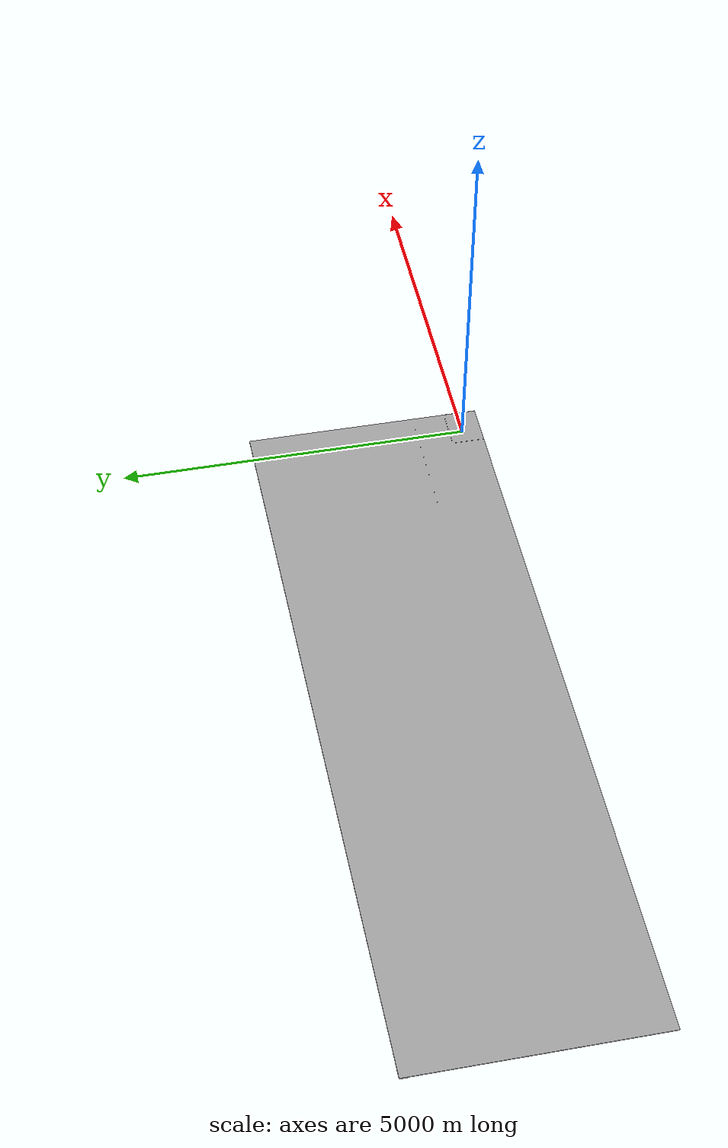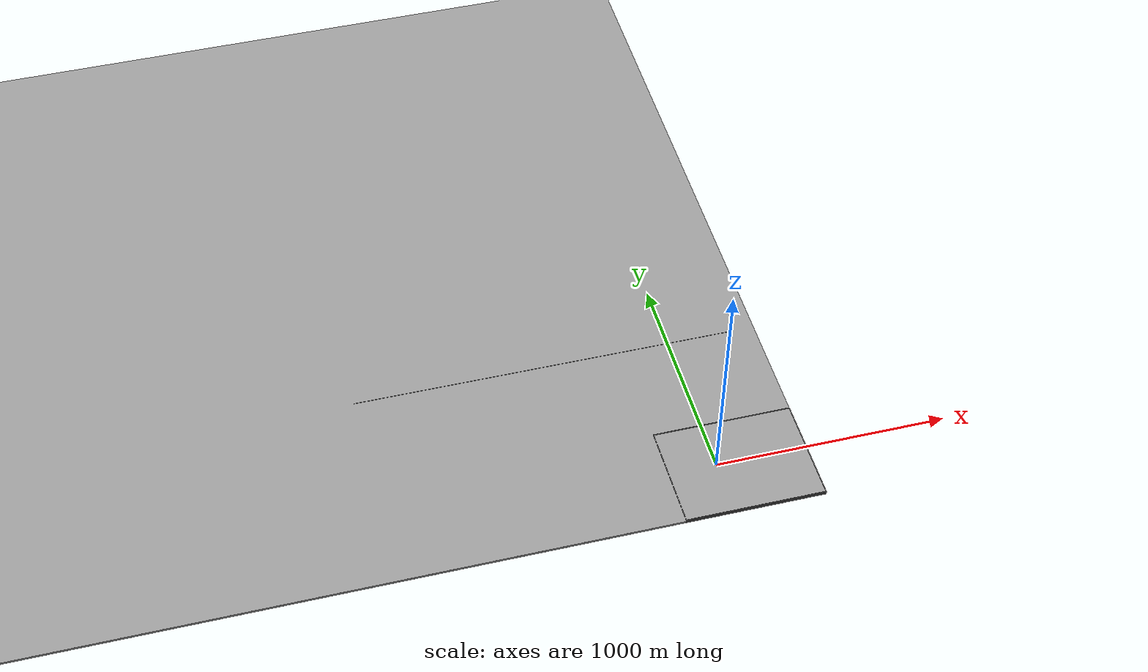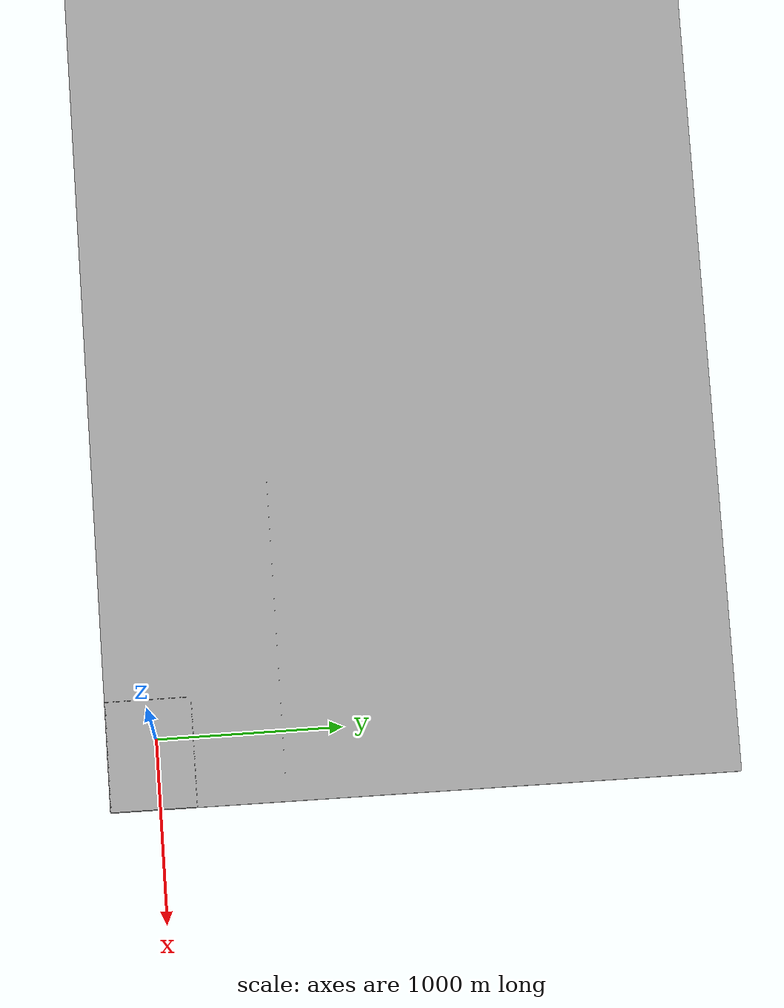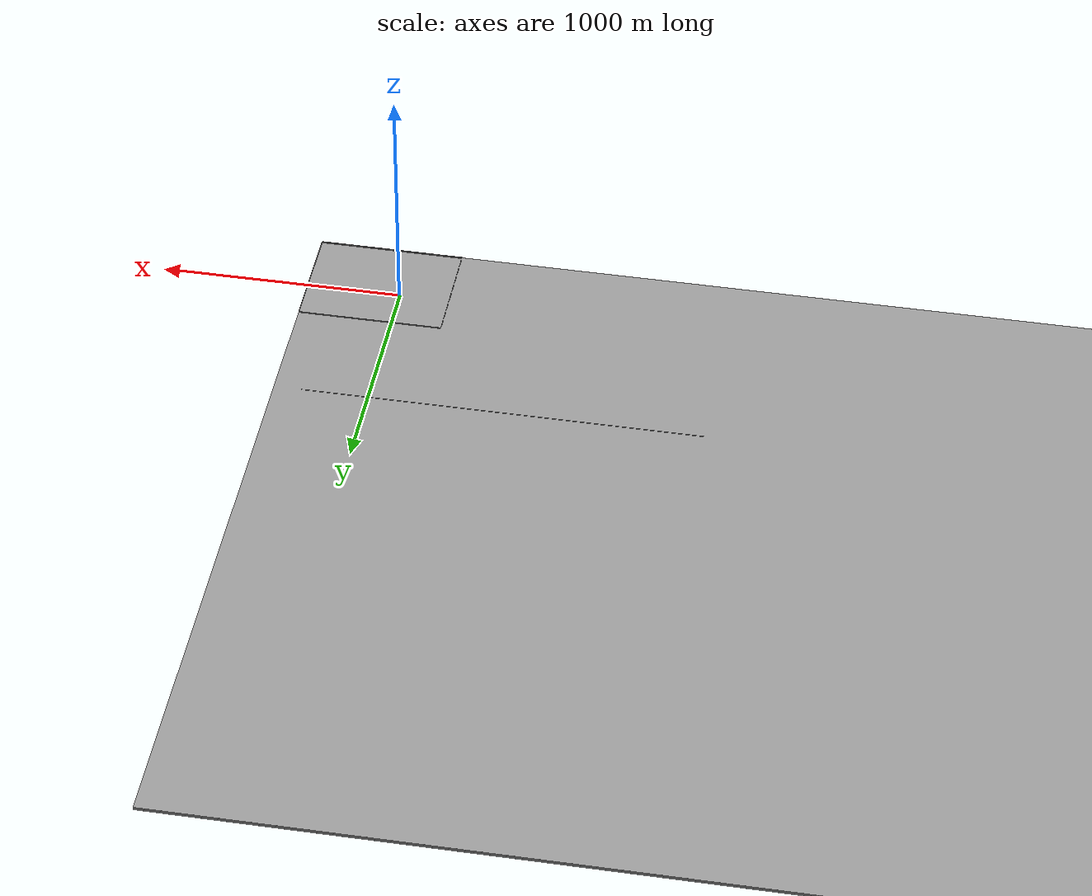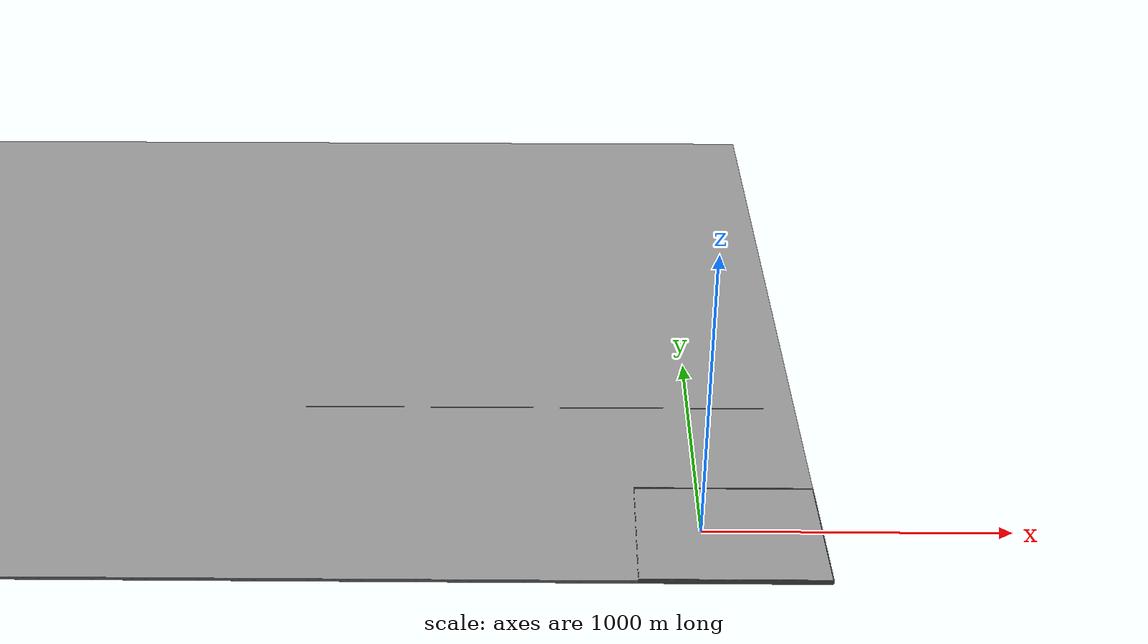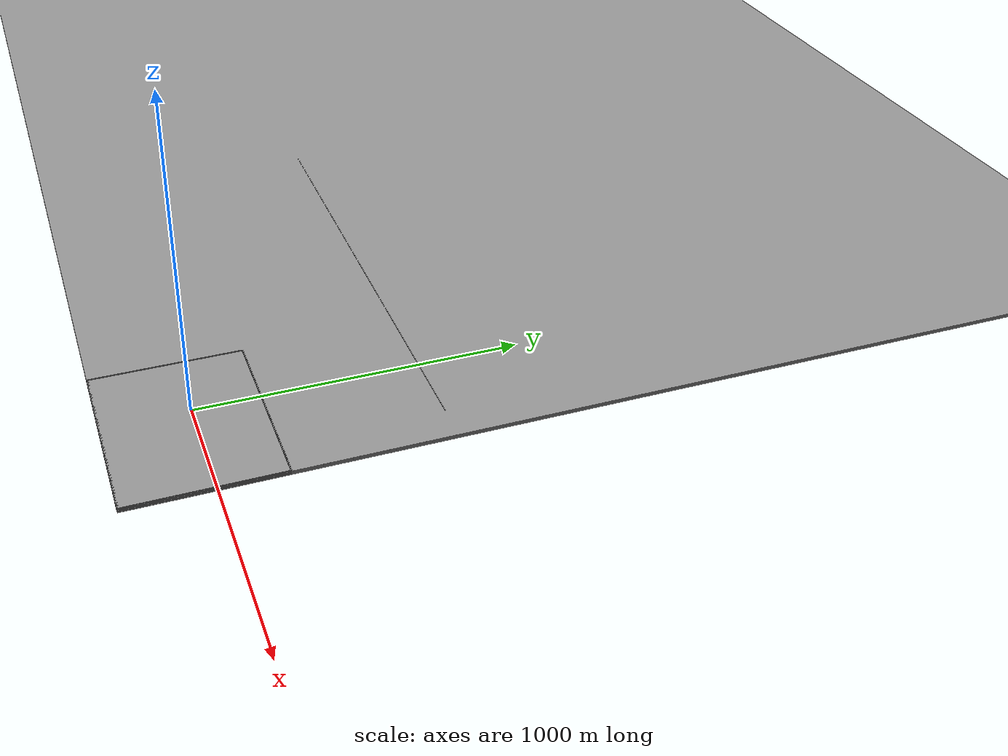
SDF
<?xml version='1.0'?>
<sdf version='1.6'>
  <model name='10floor'>
    <pose frame=''>-4881.98 1418.69 0 0 -0 0</pose>
    <link name='Floor_0'>
      <collision name='Floor_0_Collision'>
        <geometry>
          <box>
            <size>208.354 120.38 0.1</size>
          </box>
        </geometry>
        <pose frame=''>0 0 0.05 0 -0 0</pose>
      </collision>
      <visual name='Floor_0_Visual'>
        <pose frame=''>0 0 0.05 0 -0 0</pose>
        <geometry>
          <box>
            <size>208.354 120.38 0.1</size>
          </box>
        </geometry>
        <material>
          <script>
            <uri>file://media/materials/scripts/gazebo.material</uri>
            <name>Gazebo/Grey</name>
          </script>
          <ambient>1 1 1 1</ambient>
        </material>
        <meta>
          <layer>1</layer>
        </meta>
      </visual>
      <pose frame=''>-5162.19 1625.07 2.5 0 -0 0</pose>
    </link>
    <link name='Floor_1'>
      <collision name='Floor_1_Collision'>
        <geometry>
          <box>
            <size>208.354 120.38 0.1</size>
          </box>
        </geometry>
        <pose frame=''>0 0 0.05 0 -0 0</pose>
      </collision>
      <visual name='Floor_1_Visual'>
        <pose frame=''>0 0 0.05 0 -0 0</pose>
        <geometry>
          <box>
            <size>208.354 120.38 0.1</size>
          </box>
        </geometry>
        <material>
          <script>
            <uri>file://media/materials/scripts/gazebo.material</uri>
            <name>Gazebo/Grey</name>
          </script>
          <ambient>1 1 1 1</ambient>
        </material>
        <meta>
          <layer>2</layer>
        </meta>
      </visual>
      <pose frame=''>-5162.19 1625.07 5 0 -0 0</pose>
    </link>
    <link name='Floor_2'>
      <collision name='Floor_2_Collision'>
        <geometry>
          <box>
            <size>208.354 120.38 0.1</size>
          </box>
        </geometry>
        <pose frame=''>0 0 0.05 0 -0 0</pose>
      </collision>
      <visual name='Floor_2_Visual'>
        <pose frame=''>0 0 0.05 0 -0 0</pose>
        <geometry>
          <box>
            <size>208.354 120.38 0.1</size>
          </box>
        </geometry>
        <material>
          <script>
            <uri>file://media/materials/scripts/gazebo.material</uri>
            <name>Gazebo/Grey</name>
          </script>
          <ambient>1 1 1 1</ambient>
        </material>
        <meta>
          <layer>3</layer>
        </meta>
      </visual>
      <pose frame=''>-5162.19 1625.07 7.5 0 -0 0</pose>
    </link>
    <link name='Floor_3'>
      <collision name='Floor_3_Collision'>
        <geometry>
          <box>
            <size>10531.8 3368.75 0.1</size>
          </box>
        </geometry>
        <pose frame=''>0 0 0.05 0 -0 0</pose>
      </collision>
      <visual name='Floor_3_Visual'>
        <pose frame=''>0 0 0.05 0 -0 0</pose>
        <geometry>
          <box>
            <size>10531.8 3368.75 0.1</size>
          </box>
        </geometry>
        <material>
          <script>
            <uri>file://media/materials/scripts/gazebo.material</uri>
            <name>Gazebo/Grey</name>
          </script>
          <ambient>1 1 1 1</ambient>
        </material>
        <meta>
          <layer>4</layer>
        </meta>
      </visual>
      <pose frame=''>-0.48819 0.888519 10 0 -0 0</pose>
    </link>
    <link name='Floor_4'>
      <collision name='Floor_4_Collision'>
        <geometry>
          <box>
            <size>10532.7 3369.32 0.1</size>
          </box>
        </geometry>
        <pose frame=''>0 0 0.05 0 -0 0</pose>
      </collision>
      <visual name='Floor_4_Visual'>
        <pose frame=''>0 0 0.05 0 -0 0</pose>
        <geometry>
          <box>
            <size>10532.7 3369.32 0.1</size>
          </box>
        </geometry>
        <material>
          <script>
            <uri>file://media/materials/scripts/gazebo.material</uri>
            <name>Gazebo/Grey</name>
          </script>
          <ambient>1 1 1 1</ambient>
        </material>
        <meta>
          <layer>5</layer>
        </meta>
      </visual>
      <pose frame=''>9.2e-05 0.603851 12.5 0 -0 0</pose>
    </link>
    <link name='Floor_5'>
      <collision name='Floor_5_Collision'>
        <geometry>
          <box>
            <size>10532.7 3370.52 0.1</size>
          </box>
        </geometry>
        <pose frame=''>0 0 0.05 0 -0 0</pose>
      </collision>
      <visual name='Floor_5_Visual'>
        <pose frame=''>0 0 0.05 0 -0 0</pose>
        <geometry>
          <box>
            <size>10532.7 3370.52 0.1</size>
          </box>
        </geometry>
        <material>
          <script>
            <uri>file://media/materials/scripts/gazebo.material</uri>
            <name>Gazebo/Grey</name>
          </script>
          <ambient>1 1 1 1</ambient>
        </material>
        <meta>
          <layer>6</layer>
        </meta>
      </visual>
      <pose frame=''>9.2e-05 -3.1e-05 15 0 -0 0</pose>
    </link>
    <link name='Floor_6'>
      <collision name='Floor_6_Collision'>
        <geometry>
          <box>
            <size>10532.7 3370.52 0.1</size>
          </box>
        </geometry>
        <pose frame=''>0 0 0.05 0 -0 0</pose>
      </collision>
      <visual name='Floor_6_Visual'>
        <pose frame=''>0 0 0.05 0 -0 0</pose>
        <geometry>
          <box>
            <size>10532.7 3370.52 0.1</size>
          </box>
        </geometry>
        <material>
          <script>
            <uri>file://media/materials/scripts/gazebo.material</uri>
            <name>Gazebo/Grey</name>
          </script>
          <ambient>1 1 1 1</ambient>
        </material>
        <meta>
          <layer>7</layer>
        </meta>
      </visual>
      <pose frame=''>9.2e-05 -3.1e-05 17.5 0 -0 0</pose>
    </link>
    <link name='Floor_7'>
      <collision name='Floor_7_Collision'>
        <geometry>
          <box>
            <size>10532.7 3370.52 0.1</size>
          </box>
        </geometry>
        <pose frame=''>0 0 0.05 0 -0 0</pose>
      </collision>
      <visual name='Floor_7_Visual'>
        <pose frame=''>0 0 0.05 0 -0 0</pose>
        <geometry>
          <box>
            <size>10532.7 3370.52 0.1</size>
          </box>
        </geometry>
        <material>
          <script>
            <uri>file://media/materials/scripts/gazebo.material</uri>
            <name>Gazebo/Grey</name>
          </script>
          <ambient>1 1 1 1</ambient>
        </material>
        <meta>
          <layer>8</layer>
        </meta>
      </visual>
      <pose frame=''>9.2e-05 -3.1e-05 20 0 -0 0</pose>
    </link>
    <link name='Floor_8'>
      <collision name='Floor_8_Collision'>
        <geometry>
          <box>
            <size>10532.7 3370.52 0.1</size>
          </box>
        </geometry>
        <pose frame=''>0 0 0.05 0 -0 0</pose>
      </collision>
      <visual name='Floor_8_Visual'>
        <pose frame=''>0 0 0.05 0 -0 0</pose>
        <geometry>
          <box>
            <size>10532.7 3370.52 0.1</size>
          </box>
        </geometry>
        <material>
          <script>
            <uri>file://media/materials/scripts/gazebo.material</uri>
            <name>Gazebo/Grey</name>
          </script>
          <ambient>1 1 1 1</ambient>
        </material>
        <meta>
          <layer>9</layer>
        </meta>
      </visual>
      <pose frame=''>9.2e-05 -3.1e-05 22.5 0 -0 0</pose>
    </link>
    <link name='Wall_1'>
      <collision name='Wall_1_Collision'>
        <geometry>
          <box>
            <size>240.5 0.15 2.5</size>
          </box>
        </geometry>
        <pose frame=''>0 0 1.25 0 -0 0</pose>
      </collision>
      <visual name='Wall_1_Visual'>
        <pose frame=''>0 0 1.25 0 -0 0</pose>
        <geometry>
          <box>
            <size>240.5 0.15 2.5</size>
          </box>
        </geometry>
        <material>
          <script>
            <uri>file://media/materials/scripts/gazebo.material</uri>
            <name>Gazebo/Grey</name>
          </script>
          <ambient>1 1 1 1</ambient>
        </material>
        <meta>
          <layer>0</layer>
        </meta>
      </visual>
      <pose frame=''>-5162.19 1625.07 0 0 -0 0.523599</pose>
    </link>
    <link name='Wall_101'>
      <collision name='Wall_101_Collision'>
        <geometry>
          <box>
            <size>240.5 0.15 2.5</size>
          </box>
        </geometry>
        <pose frame=''>0 0 1.25 0 -0 0</pose>
      </collision>
      <visual name='Wall_101_Visual'>
        <pose frame=''>0 0 1.25 0 -0 0</pose>
        <geometry>
          <box>
            <size>240.5 0.15 2.5</size>
          </box>
        </geometry>
        <material>
          <script>
            <uri>file://media/materials/scripts/gazebo.material</uri>
            <name>Gazebo/Grey</name>
          </script>
          <ambient>1 1 1 1</ambient>
        </material>
        <meta>
          <layer>9</layer>
        </meta>
      </visual>
      <pose frame=''>-5162.19 1625.07 22.5 0 -0 0.523599</pose>
    </link>
    <link name='Wall_102'>
      <collision name='Wall_102_Collision'>
        <geometry>
          <box>
            <size>1663.25 0.15 2.5</size>
          </box>
        </geometry>
        <pose frame=''>0 0 1.25 0 -0 0</pose>
      </collision>
      <visual name='Wall_102_Visual'>
        <pose frame=''>0 0 1.25 0 -0 0</pose>
        <geometry>
          <box>
            <size>1663.25 0.15 2.5</size>
          </box>
        </geometry>
        <material>
          <script>
            <uri>file://media/materials/scripts/gazebo.material</uri>
            <name>Gazebo/Grey</name>
          </script>
          <ambient>1 1 1 1</ambient>
        </material>
        <meta>
          <layer>9</layer>
        </meta>
      </visual>
      <pose frame=''>4321.41 -743.457 22.5 0 -0 0</pose>
    </link>
    <link name='Wall_103'>
      <collision name='Wall_103_Collision'>
        <geometry>
          <box>
            <size>1264.75 0.15 2.5</size>
          </box>
        </geometry>
        <pose frame=''>0 0 1.25 0 -0 0</pose>
      </collision>
      <visual name='Wall_103_Visual'>
        <pose frame=''>0 0 1.25 0 -0 0</pose>
        <geometry>
          <box>
            <size>1264.75 0.15 2.5</size>
          </box>
        </geometry>
        <material>
          <script>
            <uri>file://media/materials/scripts/gazebo.material</uri>
            <name>Gazebo/Grey</name>
          </script>
          <ambient>1 1 1 1</ambient>
        </material>
        <meta>
          <layer>9</layer>
        </meta>
      </visual>
      <pose frame=''>4520.66 -743.457 22.5 0 -0 3.14159</pose>
    </link>
    <link name='Wall_104'>
      <collision name='Wall_104_Collision'>
        <geometry>
          <box>
            <size>537.5 0.15 2.5</size>
          </box>
        </geometry>
        <pose frame=''>0 0 1.25 0 -0 0</pose>
      </collision>
      <visual name='Wall_104_Visual'>
        <pose frame=''>0 0 1.25 0 -0 0</pose>
        <geometry>
          <box>
            <size>537.5 0.15 2.5</size>
          </box>
        </geometry>
        <material>
          <script>
            <uri>file://media/materials/scripts/gazebo.material</uri>
            <name>Gazebo/Grey</name>
          </script>
          <ambient>1 1 1 1</ambient>
        </material>
        <meta>
          <layer>9</layer>
        </meta>
      </visual>
      <pose frame=''>4996.64 -1219.06 22.5 0 -0 0</pose>
    </link>
    <link name='Wall_105'>
      <collision name='Wall_105_Collision'>
        <geometry>
          <box>
            <size>464.5 0.15 2.5</size>
          </box>
        </geometry>
        <pose frame=''>0 0 1.25 0 -0 0</pose>
      </collision>
      <visual name='Wall_105_Visual'>
        <pose frame=''>0 0 1.25 0 -0 0</pose>
        <geometry>
          <box>
            <size>464.5 0.15 2.5</size>
          </box>
        </geometry>
        <material>
          <script>
            <uri>file://media/materials/scripts/gazebo.material</uri>
            <name>Gazebo/Grey</name>
          </script>
          <ambient>1 1 1 1</ambient>
        </material>
        <meta>
          <layer>9</layer>
        </meta>
      </visual>
      <pose frame=''>5265.32 -1451.24 22.5 0 -0 -1.5708</pose>
    </link>
    <link name='Wall_106'>
      <collision name='Wall_106_Collision'>
        <geometry>
          <box>
            <size>596.75 0.15 2.5</size>
          </box>
        </geometry>
        <pose frame=''>0 0 1.25 0 -0 0</pose>
      </collision>
      <visual name='Wall_106_Visual'>
        <pose frame=''>0 0 1.25 0 -0 0</pose>
        <geometry>
          <box>
            <size>596.75 0.15 2.5</size>
          </box>
        </geometry>
        <material>
          <script>
            <uri>file://media/materials/scripts/gazebo.material</uri>
            <name>Gazebo/Grey</name>
          </script>
          <ambient>1 1 1 1</ambient>
        </material>
        <meta>
          <layer>9</layer>
        </meta>
      </visual>
      <pose frame=''>4967.02 -1683.41 22.5 0 -0 3.14159</pose>
    </link>
    <link name='Wall_107'>
      <collision name='Wall_107_Collision'>
        <geometry>
          <box>
            <size>464.25 0.15 2.5</size>
          </box>
        </geometry>
        <pose frame=''>0 0 1.25 0 -0 0</pose>
      </collision>
      <visual name='Wall_107_Visual'>
        <pose frame=''>0 0 1.25 0 -0 0</pose>
        <geometry>
          <box>
            <size>464.25 0.15 2.5</size>
          </box>
        </geometry>
        <material>
          <script>
            <uri>file://media/materials/scripts/gazebo.material</uri>
            <name>Gazebo/Grey</name>
          </script>
          <ambient>1 1 1 1</ambient>
        </material>
        <meta>
          <layer>9</layer>
        </meta>
      </visual>
      <pose frame=''>4668.72 -1451.36 22.5 0 -0 1.5708</pose>
    </link>
    <link name='Wall_108'>
      <collision name='Wall_108_Collision'>
        <geometry>
          <box>
            <size>65 0.15 2.5</size>
          </box>
        </geometry>
        <pose frame=''>0 0 1.25 0 -0 0</pose>
      </collision>
      <visual name='Wall_108_Visual'>
        <pose frame=''>0 0 1.25 0 -0 0</pose>
        <geometry>
          <box>
            <size>65 0.15 2.5</size>
          </box>
        </geometry>
        <material>
          <script>
            <uri>file://media/materials/scripts/gazebo.material</uri>
            <name>Gazebo/Grey</name>
          </script>
          <ambient>1 1 1 1</ambient>
        </material>
        <meta>
          <layer>9</layer>
        </meta>
      </visual>
      <pose frame=''>4701.14 -1219.31 22.5 0 -0 0</pose>
    </link>
    <link name='Wall_109'>
      <collision name='Wall_109_Collision'>
        <geometry>
          <box>
            <size>598.25 0.15 2.5</size>
          </box>
        </geometry>
        <pose frame=''>0 0 1.25 0 -0 0</pose>
      </collision>
      <visual name='Wall_109_Visual'>
        <pose frame=''>0 0 1.25 0 -0 0</pose>
        <geometry>
          <box>
            <size>598.25 0.15 2.5</size>
          </box>
        </geometry>
        <material>
          <script>
            <uri>file://media/materials/scripts/gazebo.material</uri>
            <name>Gazebo/Grey</name>
          </script>
          <ambient>1 1 1 1</ambient>
        </material>
        <meta>
          <layer>9</layer>
        </meta>
      </visual>
      <pose frame=''>4967.25 -1219.63 22.5 0 -0 0</pose>
    </link>
    <link name='Wall_110'>
      <collision name='Wall_110_Collision'>
        <geometry>
          <box>
            <size>464.5 0.15 2.5</size>
          </box>
        </geometry>
        <pose frame=''>0 0 1.25 0 -0 0</pose>
      </collision>
      <visual name='Wall_110_Visual'>
        <pose frame=''>0 0 1.25 0 -0 0</pose>
        <geometry>
          <box>
            <size>464.5 0.15 2.5</size>
          </box>
        </geometry>
        <material>
          <script>
            <uri>file://media/materials/scripts/gazebo.material</uri>
            <name>Gazebo/Grey</name>
          </script>
          <ambient>1 1 1 1</ambient>
        </material>
        <meta>
          <layer>9</layer>
        </meta>
      </visual>
      <pose frame=''>5266.3 -1451.8 22.5 0 -0 -1.5708</pose>
    </link>
    <link name='Wall_111'>
      <collision name='Wall_111_Collision'>
        <geometry>
          <box>
            <size>599.25 0.15 2.5</size>
          </box>
        </geometry>
        <pose frame=''>0 0 1.25 0 -0 0</pose>
      </collision>
      <visual name='Wall_111_Visual'>
        <pose frame=''>0 0 1.25 0 -0 0</pose>
        <geometry>
          <box>
            <size>599.25 0.15 2.5</size>
          </box>
        </geometry>
        <material>
          <script>
            <uri>file://media/materials/scripts/gazebo.material</uri>
            <name>Gazebo/Grey</name>
          </script>
          <ambient>1 1 1 1</ambient>
        </material>
        <meta>
          <layer>9</layer>
        </meta>
      </visual>
      <pose frame=''>4966.75 -1683.98 22.5 0 -0 3.14159</pose>
    </link>
    <link name='Wall_112'>
      <collision name='Wall_112_Collision'>
        <geometry>
          <box>
            <size>462.75 0.15 2.5</size>
          </box>
        </geometry>
        <pose frame=''>0 0 1.25 0 -0 0</pose>
      </collision>
      <visual name='Wall_112_Visual'>
        <pose frame=''>0 0 1.25 0 -0 0</pose>
        <geometry>
          <box>
            <size>462.75 0.15 2.5</size>
          </box>
        </geometry>
        <material>
          <script>
            <uri>file://media/materials/scripts/gazebo.material</uri>
            <name>Gazebo/Grey</name>
          </script>
          <ambient>1 1 1 1</ambient>
        </material>
        <meta>
          <layer>9</layer>
        </meta>
      </visual>
      <pose frame=''>4667.2 -1452.68 22.5 0 -0 1.5708</pose>
    </link>
    <link name='Wall_113'>
      <collision name='Wall_113_Collision'>
        <geometry>
          <box>
            <size>598.75 0.15 2.5</size>
          </box>
        </geometry>
        <pose frame=''>0 0 1.25 0 -0 0</pose>
      </collision>
      <visual name='Wall_113_Visual'>
        <pose frame=''>0 0 1.25 0 -0 0</pose>
        <geometry>
          <box>
            <size>598.75 0.15 2.5</size>
          </box>
        </geometry>
        <material>
          <script>
            <uri>file://media/materials/scripts/gazebo.material</uri>
            <name>Gazebo/Grey</name>
          </script>
          <ambient>1 1 1 1</ambient>
        </material>
        <meta>
          <layer>9</layer>
        </meta>
      </visual>
      <pose frame=''>4966.5 -1221.38 22.5 0 -0 0</pose>
    </link>
    <link name='Wall_114'>
      <collision name='Wall_114_Collision'>
        <geometry>
          <box>
            <size>596.5 0.15 2.5</size>
          </box>
        </geometry>
        <pose frame=''>0 0 1.25 0 -0 0</pose>
      </collision>
      <visual name='Wall_114_Visual'>
        <pose frame=''>0 0 1.25 0 -0 0</pose>
        <geometry>
          <box>
            <size>596.5 0.15 2.5</size>
          </box>
        </geometry>
        <material>
          <script>
            <uri>file://media/materials/scripts/gazebo.material</uri>
            <name>Gazebo/Grey</name>
          </script>
          <ambient>1 1 1 1</ambient>
        </material>
        <meta>
          <layer>9</layer>
        </meta>
      </visual>
      <pose frame=''>4966.94 -1221.34 22.5 0 -0 0</pose>
    </link>
    <link name='Wall_115'>
      <collision name='Wall_115_Collision'>
        <geometry>
          <box>
            <size>464 0.15 2.5</size>
          </box>
        </geometry>
        <pose frame=''>0 0 1.25 0 -0 0</pose>
      </collision>
      <visual name='Wall_115_Visual'>
        <pose frame=''>0 0 1.25 0 -0 0</pose>
        <geometry>
          <box>
            <size>464 0.15 2.5</size>
          </box>
        </geometry>
        <material>
          <script>
            <uri>file://media/materials/scripts/gazebo.material</uri>
            <name>Gazebo/Grey</name>
          </script>
          <ambient>1 1 1 1</ambient>
        </material>
        <meta>
          <layer>9</layer>
        </meta>
      </visual>
      <pose frame=''>5265.12 -1453.26 22.5 0 -0 -1.5708</pose>
    </link>
    <link name='Wall_116'>
      <collision name='Wall_116_Collision'>
        <geometry>
          <box>
            <size>597 0.15 2.5</size>
          </box>
        </geometry>
        <pose frame=''>0 0 1.25 0 -0 0</pose>
      </collision>
      <visual name='Wall_116_Visual'>
        <pose frame=''>0 0 1.25 0 -0 0</pose>
        <geometry>
          <box>
            <size>597 0.15 2.5</size>
          </box>
        </geometry>
        <material>
          <script>
            <uri>file://media/materials/scripts/gazebo.material</uri>
            <name>Gazebo/Grey</name>
          </script>
          <ambient>1 1 1 1</ambient>
        </material>
        <meta>
          <layer>9</layer>
        </meta>
      </visual>
      <pose frame=''>4966.69 -1685.19 22.5 0 -0 3.14159</pose>
    </link>
    <link name='Wall_117'>
      <collision name='Wall_117_Collision'>
        <geometry>
          <box>
            <size>465 0.15 2.5</size>
          </box>
        </geometry>
        <pose frame=''>0 0 1.25 0 -0 0</pose>
      </collision>
      <visual name='Wall_117_Visual'>
        <pose frame=''>0 0 1.25 0 -0 0</pose>
        <geometry>
          <box>
            <size>465 0.15 2.5</size>
          </box>
        </geometry>
        <material>
          <script>
            <uri>file://media/materials/scripts/gazebo.material</uri>
            <name>Gazebo/Grey</name>
          </script>
          <ambient>1 1 1 1</ambient>
        </material>
        <meta>
          <layer>9</layer>
        </meta>
      </visual>
      <pose frame=''>4668.27 -1452.76 22.5 0 -0 1.5708</pose>
    </link>
    <link name='Wall_118'>
      <collision name='Wall_118_Collision'>
        <geometry>
          <box>
            <size>598.25 0.15 2.5</size>
          </box>
        </geometry>
        <pose frame=''>0 0 1.25 0 -0 0</pose>
      </collision>
      <visual name='Wall_118_Visual'>
        <pose frame=''>0 0 1.25 0 -0 0</pose>
        <geometry>
          <box>
            <size>598.25 0.15 2.5</size>
          </box>
        </geometry>
        <material>
          <script>
            <uri>file://media/materials/scripts/gazebo.material</uri>
            <name>Gazebo/Grey</name>
          </script>
          <ambient>1 1 1 1</ambient>
        </material>
        <meta>
          <layer>9</layer>
        </meta>
      </visual>
      <pose frame=''>4967.25 -1221.34 22.5 0 -0 0</pose>
    </link>
    <link name='Wall_119'>
      <collision name='Wall_119_Collision'>
        <geometry>
          <box>
            <size>458.75 0.15 2.5</size>
          </box>
        </geometry>
        <pose frame=''>0 0 1.25 0 -0 0</pose>
      </collision>
      <visual name='Wall_119_Visual'>
        <pose frame=''>0 0 1.25 0 -0 0</pose>
        <geometry>
          <box>
            <size>458.75 0.15 2.5</size>
          </box>
        </geometry>
        <material>
          <script>
            <uri>file://media/materials/scripts/gazebo.material</uri>
            <name>Gazebo/Grey</name>
          </script>
          <ambient>1 1 1 1</ambient>
        </material>
        <meta>
          <layer>9</layer>
        </meta>
      </visual>
      <pose frame=''>5266.3 -1450.64 22.5 0 -0 -1.5708</pose>
    </link>
    <link name='Wall_120'>
      <collision name='Wall_120_Collision'>
        <geometry>
          <box>
            <size>597.5 0.15 2.5</size>
          </box>
        </geometry>
        <pose frame=''>0 0 1.25 0 -0 0</pose>
      </collision>
      <visual name='Wall_120_Visual'>
        <pose frame=''>0 0 1.25 0 -0 0</pose>
        <geometry>
          <box>
            <size>597.5 0.15 2.5</size>
          </box>
        </geometry>
        <material>
          <script>
            <uri>file://media/materials/scripts/gazebo.material</uri>
            <name>Gazebo/Grey</name>
          </script>
          <ambient>1 1 1 1</ambient>
        </material>
        <meta>
          <layer>9</layer>
        </meta>
      </visual>
      <pose frame=''>4967.62 -1679.94 22.5 0 -0 3.14159</pose>
    </link>
    <link name='Wall_121'>
      <collision name='Wall_121_Collision'>
        <geometry>
          <box>
            <size>458 0.15 2.5</size>
          </box>
        </geometry>
        <pose frame=''>0 0 1.25 0 -0 0</pose>
      </collision>
      <visual name='Wall_121_Visual'>
        <pose frame=''>0 0 1.25 0 -0 0</pose>
        <geometry>
          <box>
            <size>458 0.15 2.5</size>
          </box>
        </geometry>
        <material>
          <script>
            <uri>file://media/materials/scripts/gazebo.material</uri>
            <name>Gazebo/Grey</name>
          </script>
          <ambient>1 1 1 1</ambient>
        </material>
        <meta>
          <layer>9</layer>
        </meta>
      </visual>
      <pose frame=''>4668.95 -1451.01 22.5 0 -0 1.5708</pose>
    </link>
    <link name='Wall_122'>
      <collision name='Wall_122_Collision'>
        <geometry>
          <box>
            <size>596.5 0.15 2.5</size>
          </box>
        </geometry>
        <pose frame=''>0 0 1.25 0 -0 0</pose>
      </collision>
      <visual name='Wall_122_Visual'>
        <pose frame=''>0 0 1.25 0 -0 0</pose>
        <geometry>
          <box>
            <size>596.5 0.15 2.5</size>
          </box>
        </geometry>
        <material>
          <script>
            <uri>file://media/materials/scripts/gazebo.material</uri>
            <name>Gazebo/Grey</name>
          </script>
          <ambient>1 1 1 1</ambient>
        </material>
        <meta>
          <layer>9</layer>
        </meta>
      </visual>
      <pose frame=''>4967.51 -1221.34 22.5 0 -0 0</pose>
    </link>
    <link name='Wall_123'>
      <collision name='Wall_123_Collision'>
        <geometry>
          <box>
            <size>461.75 0.15 2.5</size>
          </box>
        </geometry>
        <pose frame=''>0 0 1.25 0 -0 0</pose>
      </collision>
      <visual name='Wall_123_Visual'>
        <pose frame=''>0 0 1.25 0 -0 0</pose>
        <geometry>
          <box>
            <size>461.75 0.15 2.5</size>
          </box>
        </geometry>
        <material>
          <script>
            <uri>file://media/materials/scripts/gazebo.material</uri>
            <name>Gazebo/Grey</name>
          </script>
          <ambient>1 1 1 1</ambient>
        </material>
        <meta>
          <layer>9</layer>
        </meta>
      </visual>
      <pose frame=''>5265.68 -1452.14 22.5 0 -0 -1.5708</pose>
    </link>
    <link name='Wall_124'>
      <collision name='Wall_124_Collision'>
        <geometry>
          <box>
            <size>597 0.15 2.5</size>
          </box>
        </geometry>
        <pose frame=''>0 0 1.25 0 -0 0</pose>
      </collision>
      <visual name='Wall_124_Visual'>
        <pose frame=''>0 0 1.25 0 -0 0</pose>
        <geometry>
          <box>
            <size>597 0.15 2.5</size>
          </box>
        </geometry>
        <material>
          <script>
            <uri>file://media/materials/scripts/gazebo.material</uri>
            <name>Gazebo/Grey</name>
          </script>
          <ambient>1 1 1 1</ambient>
        </material>
        <meta>
          <layer>9</layer>
        </meta>
      </visual>
      <pose frame=''>4967.26 -1682.94 22.5 0 -0 3.14159</pose>
    </link>
    <link name='Wall_125'>
      <collision name='Wall_125_Collision'>
        <geometry>
          <box>
            <size>461 0.15 2.5</size>
          </box>
        </geometry>
        <pose frame=''>0 0 1.25 0 -0 0</pose>
      </collision>
      <visual name='Wall_125_Visual'>
        <pose frame=''>0 0 1.25 0 -0 0</pose>
        <geometry>
          <box>
            <size>461 0.15 2.5</size>
          </box>
        </geometry>
        <material>
          <script>
            <uri>file://media/materials/scripts/gazebo.material</uri>
            <name>Gazebo/Grey</name>
          </script>
          <ambient>1 1 1 1</ambient>
        </material>
        <meta>
          <layer>9</layer>
        </meta>
      </visual>
      <pose frame=''>4668.83 -1452.51 22.5 0 -0 1.5708</pose>
    </link>
    <link name='Wall_126'>
      <collision name='Wall_126_Collision'>
        <geometry>
          <box>
            <size>595.5 0.15 2.5</size>
          </box>
        </geometry>
        <pose frame=''>0 0 1.25 0 -0 0</pose>
      </collision>
      <visual name='Wall_126_Visual'>
        <pose frame=''>0 0 1.25 0 -0 0</pose>
        <geometry>
          <box>
            <size>595.5 0.15 2.5</size>
          </box>
        </geometry>
        <material>
          <script>
            <uri>file://media/materials/scripts/gazebo.material</uri>
            <name>Gazebo/Grey</name>
          </script>
          <ambient>1 1 1 1</ambient>
        </material>
        <meta>
          <layer>9</layer>
        </meta>
      </visual>
      <pose frame=''>4967.01 -1221.91 22.5 0 -0 0</pose>
    </link>
    <link name='Wall_127'>
      <collision name='Wall_127_Collision'>
        <geometry>
          <box>
            <size>460.5 0.15 2.5</size>
          </box>
        </geometry>
        <pose frame=''>0 0 1.25 0 -0 0</pose>
      </collision>
      <visual name='Wall_127_Visual'>
        <pose frame=''>0 0 1.25 0 -0 0</pose>
        <geometry>
          <box>
            <size>460.5 0.15 2.5</size>
          </box>
        </geometry>
        <material>
          <script>
            <uri>file://media/materials/scripts/gazebo.material</uri>
            <name>Gazebo/Grey</name>
          </script>
          <ambient>1 1 1 1</ambient>
        </material>
        <meta>
          <layer>9</layer>
        </meta>
      </visual>
      <pose frame=''>5264.68 -1452.08 22.5 0 -0 -1.5708</pose>
    </link>
    <link name='Wall_128'>
      <collision name='Wall_128_Collision'>
        <geometry>
          <box>
            <size>596.5 0.15 2.5</size>
          </box>
        </geometry>
        <pose frame=''>0 0 1.25 0 -0 0</pose>
      </collision>
      <visual name='Wall_128_Visual'>
        <pose frame=''>0 0 1.25 0 -0 0</pose>
        <geometry>
          <box>
            <size>596.5 0.15 2.5</size>
          </box>
        </geometry>
        <material>
          <script>
            <uri>file://media/materials/scripts/gazebo.material</uri>
            <name>Gazebo/Grey</name>
          </script>
          <ambient>1 1 1 1</ambient>
        </material>
        <meta>
          <layer>9</layer>
        </meta>
      </visual>
      <pose frame=''>4966.51 -1682.26 22.5 0 -0 3.14159</pose>
    </link>
    <link name='Wall_129'>
      <collision name='Wall_129_Collision'>
        <geometry>
          <box>
            <size>460.25 0.15 2.5</size>
          </box>
        </geometry>
        <pose frame=''>0 0 1.25 0 -0 0</pose>
      </collision>
      <visual name='Wall_129_Visual'>
        <pose frame=''>0 0 1.25 0 -0 0</pose>
        <geometry>
          <box>
            <size>460.25 0.15 2.5</size>
          </box>
        </geometry>
        <material>
          <script>
            <uri>file://media/materials/scripts/gazebo.material</uri>
            <name>Gazebo/Grey</name>
          </script>
          <ambient>1 1 1 1</ambient>
        </material>
        <meta>
          <layer>9</layer>
        </meta>
      </visual>
      <pose frame=''>4668.33 -1452.21 22.5 0 -0 1.5708</pose>
    </link>
    <link name='Wall_15'>
      <collision name='Wall_15_Collision'>
        <geometry>
          <box>
            <size>537.5 0.15 2.5</size>
          </box>
        </geometry>
        <pose frame=''>0 0 1.25 0 -0 0</pose>
      </collision>
      <visual name='Wall_15_Visual'>
        <pose frame=''>0 0 1.25 0 -0 0</pose>
        <geometry>
          <box>
            <size>537.5 0.15 2.5</size>
          </box>
        </geometry>
        <material>
          <script>
            <uri>file://media/materials/scripts/gazebo.material</uri>
            <name>Gazebo/Grey</name>
          </script>
          <ambient>1 1 1 1</ambient>
        </material>
        <meta>
          <layer>4</layer>
        </meta>
      </visual>
      <pose frame=''>4996.64 -1219.06 10 0 -0 0</pose>
    </link>
    <link name='Wall_16'>
      <collision name='Wall_16_Collision'>
        <geometry>
          <box>
            <size>464.5 0.15 2.5</size>
          </box>
        </geometry>
        <pose frame=''>0 0 1.25 0 -0 0</pose>
      </collision>
      <visual name='Wall_16_Visual'>
        <pose frame=''>0 0 1.25 0 -0 0</pose>
        <geometry>
          <box>
            <size>464.5 0.15 2.5</size>
          </box>
        </geometry>
        <material>
          <script>
            <uri>file://media/materials/scripts/gazebo.material</uri>
            <name>Gazebo/Grey</name>
          </script>
          <ambient>1 1 1 1</ambient>
        </material>
        <meta>
          <layer>4</layer>
        </meta>
      </visual>
      <pose frame=''>5265.32 -1451.24 10 0 -0 -1.5708</pose>
    </link>
    <link name='Wall_17'>
      <collision name='Wall_17_Collision'>
        <geometry>
          <box>
            <size>596.75 0.15 2.5</size>
          </box>
        </geometry>
        <pose frame=''>0 0 1.25 0 -0 0</pose>
      </collision>
      <visual name='Wall_17_Visual'>
        <pose frame=''>0 0 1.25 0 -0 0</pose>
        <geometry>
          <box>
            <size>596.75 0.15 2.5</size>
          </box>
        </geometry>
        <material>
          <script>
            <uri>file://media/materials/scripts/gazebo.material</uri>
            <name>Gazebo/Grey</name>
          </script>
          <ambient>1 1 1 1</ambient>
        </material>
        <meta>
          <layer>4</layer>
        </meta>
      </visual>
      <pose frame=''>4967.02 -1683.41 10 0 -0 3.14159</pose>
    </link>
    <link name='Wall_18'>
      <collision name='Wall_18_Collision'>
        <geometry>
          <box>
            <size>464.25 0.15 2.5</size>
          </box>
        </geometry>
        <pose frame=''>0 0 1.25 0 -0 0</pose>
      </collision>
      <visual name='Wall_18_Visual'>
        <pose frame=''>0 0 1.25 0 -0 0</pose>
        <geometry>
          <box>
            <size>464.25 0.15 2.5</size>
          </box>
        </geometry>
        <material>
          <script>
            <uri>file://media/materials/scripts/gazebo.material</uri>
            <name>Gazebo/Grey</name>
          </script>
          <ambient>1 1 1 1</ambient>
        </material>
        <meta>
          <layer>4</layer>
        </meta>
      </visual>
      <pose frame=''>4668.72 -1451.36 10 0 -0 1.5708</pose>
    </link>
    <link name='Wall_19'>
      <collision name='Wall_19_Collision'>
        <geometry>
          <box>
            <size>65 0.15 2.5</size>
          </box>
        </geometry>
        <pose frame=''>0 0 1.25 0 -0 0</pose>
      </collision>
      <visual name='Wall_19_Visual'>
        <pose frame=''>0 0 1.25 0 -0 0</pose>
        <geometry>
          <box>
            <size>65 0.15 2.5</size>
          </box>
        </geometry>
        <material>
          <script>
            <uri>file://media/materials/scripts/gazebo.material</uri>
            <name>Gazebo/Grey</name>
          </script>
          <ambient>1 1 1 1</ambient>
        </material>
        <meta>
          <layer>4</layer>
        </meta>
      </visual>
      <pose frame=''>4701.14 -1219.31 10 0 -0 0</pose>
    </link>
    <link name='Wall_21'>
      <collision name='Wall_21_Collision'>
        <geometry>
          <box>
            <size>240.5 0.15 2.5</size>
          </box>
        </geometry>
        <pose frame=''>0 0 1.25 0 -0 0</pose>
      </collision>
      <visual name='Wall_21_Visual'>
        <pose frame=''>0 0 1.25 0 -0 0</pose>
        <geometry>
          <box>
            <size>240.5 0.15 2.5</size>
          </box>
        </geometry>
        <material>
          <script>
            <uri>file://media/materials/scripts/gazebo.material</uri>
            <name>Gazebo/Grey</name>
          </script>
          <ambient>1 1 1 1</ambient>
        </material>
        <meta>
          <layer>5</layer>
        </meta>
      </visual>
      <pose frame=''>-5162.19 1625.07 12.5 0 -0 0.523599</pose>
    </link>
    <link name='Wall_22'>
      <collision name='Wall_22_Collision'>
        <geometry>
          <box>
            <size>1663.25 0.15 2.5</size>
          </box>
        </geometry>
        <pose frame=''>0 0 1.25 0 -0 0</pose>
      </collision>
      <visual name='Wall_22_Visual'>
        <pose frame=''>0 0 1.25 0 -0 0</pose>
        <geometry>
          <box>
            <size>1663.25 0.15 2.5</size>
          </box>
        </geometry>
        <material>
          <script>
            <uri>file://media/materials/scripts/gazebo.material</uri>
            <name>Gazebo/Grey</name>
          </script>
          <ambient>1 1 1 1</ambient>
        </material>
        <meta>
          <layer>5</layer>
        </meta>
      </visual>
      <pose frame=''>4321.41 -743.457 12.5 0 -0 0</pose>
    </link>
    <link name='Wall_23'>
      <collision name='Wall_23_Collision'>
        <geometry>
          <box>
            <size>1264.75 0.15 2.5</size>
          </box>
        </geometry>
        <pose frame=''>0 0 1.25 0 -0 0</pose>
      </collision>
      <visual name='Wall_23_Visual'>
        <pose frame=''>0 0 1.25 0 -0 0</pose>
        <geometry>
          <box>
            <size>1264.75 0.15 2.5</size>
          </box>
        </geometry>
        <material>
          <script>
            <uri>file://media/materials/scripts/gazebo.material</uri>
            <name>Gazebo/Grey</name>
          </script>
          <ambient>1 1 1 1</ambient>
        </material>
        <meta>
          <layer>5</layer>
        </meta>
      </visual>
      <pose frame=''>4520.66 -743.457 12.5 0 -0 3.14159</pose>
    </link>
    <link name='Wall_24'>
      <collision name='Wall_24_Collision'>
        <geometry>
          <box>
            <size>537.5 0.15 2.5</size>
          </box>
        </geometry>
        <pose frame=''>0 0 1.25 0 -0 0</pose>
      </collision>
      <visual name='Wall_24_Visual'>
        <pose frame=''>0 0 1.25 0 -0 0</pose>
        <geometry>
          <box>
            <size>537.5 0.15 2.5</size>
          </box>
        </geometry>
        <material>
          <script>
            <uri>file://media/materials/scripts/gazebo.material</uri>
            <name>Gazebo/Grey</name>
          </script>
          <ambient>1 1 1 1</ambient>
        </material>
        <meta>
          <layer>5</layer>
        </meta>
      </visual>
      <pose frame=''>4996.64 -1219.06 12.5 0 -0 0</pose>
    </link>
    <link name='Wall_25'>
      <collision name='Wall_25_Collision'>
        <geometry>
          <box>
            <size>464.5 0.15 2.5</size>
          </box>
        </geometry>
        <pose frame=''>0 0 1.25 0 -0 0</pose>
      </collision>
      <visual name='Wall_25_Visual'>
        <pose frame=''>0 0 1.25 0 -0 0</pose>
        <geometry>
          <box>
            <size>464.5 0.15 2.5</size>
          </box>
        </geometry>
        <material>
          <script>
            <uri>file://media/materials/scripts/gazebo.material</uri>
            <name>Gazebo/Grey</name>
          </script>
          <ambient>1 1 1 1</ambient>
        </material>
        <meta>
          <layer>5</layer>
        </meta>
      </visual>
      <pose frame=''>5265.32 -1451.24 12.5 0 -0 -1.5708</pose>
    </link>
    <link name='Wall_26'>
      <collision name='Wall_26_Collision'>
        <geometry>
          <box>
            <size>596.75 0.15 2.5</size>
          </box>
        </geometry>
        <pose frame=''>0 0 1.25 0 -0 0</pose>
      </collision>
      <visual name='Wall_26_Visual'>
        <pose frame=''>0 0 1.25 0 -0 0</pose>
        <geometry>
          <box>
            <size>596.75 0.15 2.5</size>
          </box>
        </geometry>
        <material>
          <script>
            <uri>file://media/materials/scripts/gazebo.material</uri>
            <name>Gazebo/Grey</name>
          </script>
          <ambient>1 1 1 1</ambient>
        </material>
        <meta>
          <layer>5</layer>
        </meta>
      </visual>
      <pose frame=''>4967.02 -1683.41 12.5 0 -0 3.14159</pose>
    </link>
    <link name='Wall_27'>
      <collision name='Wall_27_Collision'>
        <geometry>
          <box>
            <size>464.25 0.15 2.5</size>
          </box>
        </geometry>
        <pose frame=''>0 0 1.25 0 -0 0</pose>
      </collision>
      <visual name='Wall_27_Visual'>
        <pose frame=''>0 0 1.25 0 -0 0</pose>
        <geometry>
          <box>
            <size>464.25 0.15 2.5</size>
          </box>
        </geometry>
        <material>
          <script>
            <uri>file://media/materials/scripts/gazebo.material</uri>
            <name>Gazebo/Grey</name>
          </script>
          <ambient>1 1 1 1</ambient>
        </material>
        <meta>
          <layer>5</layer>
        </meta>
      </visual>
      <pose frame=''>4668.72 -1451.36 12.5 0 -0 1.5708</pose>
    </link>
    <link name='Wall_28'>
      <collision name='Wall_28_Collision'>
        <geometry>
          <box>
            <size>65 0.15 2.5</size>
          </box>
        </geometry>
        <pose frame=''>0 0 1.25 0 -0 0</pose>
      </collision>
      <visual name='Wall_28_Visual'>
        <pose frame=''>0 0 1.25 0 -0 0</pose>
        <geometry>
          <box>
            <size>65 0.15 2.5</size>
          </box>
        </geometry>
        <material>
          <script>
            <uri>file://media/materials/scripts/gazebo.material</uri>
            <name>Gazebo/Grey</name>
          </script>
          <ambient>1 1 1 1</ambient>
        </material>
        <meta>
          <layer>5</layer>
        </meta>
      </visual>
      <pose frame=''>4701.14 -1219.31 12.5 0 -0 0</pose>
    </link>
    <link name='Wall_29'>
      <collision name='Wall_29_Collision'>
        <geometry>
          <box>
            <size>598.25 0.15 2.5</size>
          </box>
        </geometry>
        <pose frame=''>0 0 1.25 0 -0 0</pose>
      </collision>
      <visual name='Wall_29_Visual'>
        <pose frame=''>0 0 1.25 0 -0 0</pose>
        <geometry>
          <box>
            <size>598.25 0.15 2.5</size>
          </box>
        </geometry>
        <material>
          <script>
            <uri>file://media/materials/scripts/gazebo.material</uri>
            <name>Gazebo/Grey</name>
          </script>
          <ambient>1 1 1 1</ambient>
        </material>
        <meta>
          <layer>5</layer>
        </meta>
      </visual>
      <pose frame=''>4967.25 -1219.63 12.5 0 -0 0</pose>
    </link>
    <link name='Wall_3'>
      <collision name='Wall_3_Collision'>
        <geometry>
          <box>
            <size>240.5 0.15 2.5</size>
          </box>
        </geometry>
        <pose frame=''>0 0 1.25 0 -0 0</pose>
      </collision>
      <visual name='Wall_3_Visual'>
        <pose frame=''>0 0 1.25 0 -0 0</pose>
        <geometry>
          <box>
            <size>240.5 0.15 2.5</size>
          </box>
        </geometry>
        <material>
          <script>
            <uri>file://media/materials/scripts/gazebo.material</uri>
            <name>Gazebo/Grey</name>
          </script>
          <ambient>1 1 1 1</ambient>
        </material>
        <meta>
          <layer>1</layer>
        </meta>
      </visual>
      <pose frame=''>-5162.19 1625.07 2.5 0 -0 0.523599</pose>
    </link>
    <link name='Wall_30'>
      <collision name='Wall_30_Collision'>
        <geometry>
          <box>
            <size>464.5 0.15 2.5</size>
          </box>
        </geometry>
        <pose frame=''>0 0 1.25 0 -0 0</pose>
      </collision>
      <visual name='Wall_30_Visual'>
        <pose frame=''>0 0 1.25 0 -0 0</pose>
        <geometry>
          <box>
            <size>464.5 0.15 2.5</size>
          </box>
        </geometry>
        <material>
          <script>
            <uri>file://media/materials/scripts/gazebo.material</uri>
            <name>Gazebo/Grey</name>
          </script>
          <ambient>1 1 1 1</ambient>
        </material>
        <meta>
          <layer>5</layer>
        </meta>
      </visual>
      <pose frame=''>5266.3 -1451.8 12.5 0 -0 -1.5708</pose>
    </link>
    <link name='Wall_31'>
      <collision name='Wall_31_Collision'>
        <geometry>
          <box>
            <size>599.25 0.15 2.5</size>
          </box>
        </geometry>
        <pose frame=''>0 0 1.25 0 -0 0</pose>
      </collision>
      <visual name='Wall_31_Visual'>
        <pose frame=''>0 0 1.25 0 -0 0</pose>
        <geometry>
          <box>
            <size>599.25 0.15 2.5</size>
          </box>
        </geometry>
        <material>
          <script>
            <uri>file://media/materials/scripts/gazebo.material</uri>
            <name>Gazebo/Grey</name>
          </script>
          <ambient>1 1 1 1</ambient>
        </material>
        <meta>
          <layer>5</layer>
        </meta>
      </visual>
      <pose frame=''>4966.75 -1683.98 12.5 0 -0 3.14159</pose>
    </link>
    <link name='Wall_32'>
      <collision name='Wall_32_Collision'>
        <geometry>
          <box>
            <size>462.75 0.15 2.5</size>
          </box>
        </geometry>
        <pose frame=''>0 0 1.25 0 -0 0</pose>
      </collision>
      <visual name='Wall_32_Visual'>
        <pose frame=''>0 0 1.25 0 -0 0</pose>
        <geometry>
          <box>
            <size>462.75 0.15 2.5</size>
          </box>
        </geometry>
        <material>
          <script>
            <uri>file://media/materials/scripts/gazebo.material</uri>
            <name>Gazebo/Grey</name>
          </script>
          <ambient>1 1 1 1</ambient>
        </material>
        <meta>
          <layer>5</layer>
        </meta>
      </visual>
      <pose frame=''>4667.2 -1452.68 12.5 0 -0 1.5708</pose>
    </link>
    <link name='Wall_33'>
      <collision name='Wall_33_Collision'>
        <geometry>
          <box>
            <size>598.75 0.15 2.5</size>
          </box>
        </geometry>
        <pose frame=''>0 0 1.25 0 -0 0</pose>
      </collision>
      <visual name='Wall_33_Visual'>
        <pose frame=''>0 0 1.25 0 -0 0</pose>
        <geometry>
          <box>
            <size>598.75 0.15 2.5</size>
          </box>
        </geometry>
        <material>
          <script>
            <uri>file://media/materials/scripts/gazebo.material</uri>
            <name>Gazebo/Grey</name>
          </script>
          <ambient>1 1 1 1</ambient>
        </material>
        <meta>
          <layer>5</layer>
        </meta>
      </visual>
      <pose frame=''>4966.5 -1221.38 12.5 0 -0 0</pose>
    </link>
    <link name='Wall_35'>
      <collision name='Wall_35_Collision'>
        <geometry>
          <box>
            <size>240.5 0.15 2.5</size>
          </box>
        </geometry>
        <pose frame=''>0 0 1.25 0 -0 0</pose>
      </collision>
      <visual name='Wall_35_Visual'>
        <pose frame=''>0 0 1.25 0 -0 0</pose>
        <geometry>
          <box>
            <size>240.5 0.15 2.5</size>
          </box>
        </geometry>
        <material>
          <script>
            <uri>file://media/materials/scripts/gazebo.material</uri>
            <name>Gazebo/Grey</name>
          </script>
          <ambient>1 1 1 1</ambient>
        </material>
        <meta>
          <layer>6</layer>
        </meta>
      </visual>
      <pose frame=''>-5162.19 1625.07 15 0 -0 0.523599</pose>
    </link>
    <link name='Wall_36'>
      <collision name='Wall_36_Collision'>
        <geometry>
          <box>
            <size>1663.25 0.15 2.5</size>
          </box>
        </geometry>
        <pose frame=''>0 0 1.25 0 -0 0</pose>
      </collision>
      <visual name='Wall_36_Visual'>
        <pose frame=''>0 0 1.25 0 -0 0</pose>
        <geometry>
          <box>
            <size>1663.25 0.15 2.5</size>
          </box>
        </geometry>
        <material>
          <script>
            <uri>file://media/materials/scripts/gazebo.material</uri>
            <name>Gazebo/Grey</name>
          </script>
          <ambient>1 1 1 1</ambient>
        </material>
        <meta>
          <layer>6</layer>
        </meta>
      </visual>
      <pose frame=''>4321.41 -743.457 15 0 -0 0</pose>
    </link>
    <link name='Wall_37'>
      <collision name='Wall_37_Collision'>
        <geometry>
          <box>
            <size>1264.75 0.15 2.5</size>
          </box>
        </geometry>
        <pose frame=''>0 0 1.25 0 -0 0</pose>
      </collision>
      <visual name='Wall_37_Visual'>
        <pose frame=''>0 0 1.25 0 -0 0</pose>
        <geometry>
          <box>
            <size>1264.75 0.15 2.5</size>
          </box>
        </geometry>
        <material>
          <script>
            <uri>file://media/materials/scripts/gazebo.material</uri>
            <name>Gazebo/Grey</name>
          </script>
          <ambient>1 1 1 1</ambient>
        </material>
        <meta>
          <layer>6</layer>
        </meta>
      </visual>
      <pose frame=''>4520.66 -743.457 15 0 -0 3.14159</pose>
    </link>
    <link name='Wall_38'>
      <collision name='Wall_38_Collision'>
        <geometry>
          <box>
            <size>537.5 0.15 2.5</size>
          </box>
        </geometry>
        <pose frame=''>0 0 1.25 0 -0 0</pose>
      </collision>
      <visual name='Wall_38_Visual'>
        <pose frame=''>0 0 1.25 0 -0 0</pose>
        <geometry>
          <box>
            <size>537.5 0.15 2.5</size>
          </box>
        </geometry>
        <material>
          <script>
            <uri>file://media/materials/scripts/gazebo.material</uri>
            <name>Gazebo/Grey</name>
          </script>
          <ambient>1 1 1 1</ambient>
        </material>
        <meta>
          <layer>6</layer>
        </meta>
      </visual>
      <pose frame=''>4996.64 -1219.06 15 0 -0 0</pose>
    </link>
    <link name='Wall_39'>
      <collision name='Wall_39_Collision'>
        <geometry>
          <box>
            <size>464.5 0.15 2.5</size>
          </box>
        </geometry>
        <pose frame=''>0 0 1.25 0 -0 0</pose>
      </collision>
      <visual name='Wall_39_Visual'>
        <pose frame=''>0 0 1.25 0 -0 0</pose>
        <geometry>
          <box>
            <size>464.5 0.15 2.5</size>
          </box>
        </geometry>
        <material>
          <script>
            <uri>file://media/materials/scripts/gazebo.material</uri>
            <name>Gazebo/Grey</name>
          </script>
          <ambient>1 1 1 1</ambient>
        </material>
        <meta>
          <layer>6</layer>
        </meta>
      </visual>
      <pose frame=''>5265.32 -1451.24 15 0 -0 -1.5708</pose>
    </link>
    <link name='Wall_4'>
      <collision name='Wall_4_Collision'>
        <geometry>
          <box>
            <size>240.5 0.15 2.5</size>
          </box>
        </geometry>
        <pose frame=''>0 0 1.25 0 -0 0</pose>
      </collision>
      <visual name='Wall_4_Visual'>
        <pose frame=''>0 0 1.25 0 -0 0</pose>
        <geometry>
          <box>
            <size>240.5 0.15 2.5</size>
          </box>
        </geometry>
        <material>
          <script>
            <uri>file://media/materials/scripts/gazebo.material</uri>
            <name>Gazebo/Grey</name>
          </script>
          <ambient>1 1 1 1</ambient>
        </material>
        <meta>
          <layer>2</layer>
        </meta>
      </visual>
      <pose frame=''>-5162.19 1625.07 5 0 -0 0.523599</pose>
    </link>
    <link name='Wall_40'>
      <collision name='Wall_40_Collision'>
        <geometry>
          <box>
            <size>596.75 0.15 2.5</size>
          </box>
        </geometry>
        <pose frame=''>0 0 1.25 0 -0 0</pose>
      </collision>
      <visual name='Wall_40_Visual'>
        <pose frame=''>0 0 1.25 0 -0 0</pose>
        <geometry>
          <box>
            <size>596.75 0.15 2.5</size>
          </box>
        </geometry>
        <material>
          <script>
            <uri>file://media/materials/scripts/gazebo.material</uri>
            <name>Gazebo/Grey</name>
          </script>
          <ambient>1 1 1 1</ambient>
        </material>
        <meta>
          <layer>6</layer>
        </meta>
      </visual>
      <pose frame=''>4967.02 -1683.41 15 0 -0 3.14159</pose>
    </link>
    <link name='Wall_41'>
      <collision name='Wall_41_Collision'>
        <geometry>
          <box>
            <size>464.25 0.15 2.5</size>
          </box>
        </geometry>
        <pose frame=''>0 0 1.25 0 -0 0</pose>
      </collision>
      <visual name='Wall_41_Visual'>
        <pose frame=''>0 0 1.25 0 -0 0</pose>
        <geometry>
          <box>
            <size>464.25 0.15 2.5</size>
          </box>
        </geometry>
        <material>
          <script>
            <uri>file://media/materials/scripts/gazebo.material</uri>
            <name>Gazebo/Grey</name>
          </script>
          <ambient>1 1 1 1</ambient>
        </material>
        <meta>
          <layer>6</layer>
        </meta>
      </visual>
      <pose frame=''>4668.72 -1451.36 15 0 -0 1.5708</pose>
    </link>
    <link name='Wall_42'>
      <collision name='Wall_42_Collision'>
        <geometry>
          <box>
            <size>65 0.15 2.5</size>
          </box>
        </geometry>
        <pose frame=''>0 0 1.25 0 -0 0</pose>
      </collision>
      <visual name='Wall_42_Visual'>
        <pose frame=''>0 0 1.25 0 -0 0</pose>
        <geometry>
          <box>
            <size>65 0.15 2.5</size>
          </box>
        </geometry>
        <material>
          <script>
            <uri>file://media/materials/scripts/gazebo.material</uri>
            <name>Gazebo/Grey</name>
          </script>
          <ambient>1 1 1 1</ambient>
        </material>
        <meta>
          <layer>6</layer>
        </meta>
      </visual>
      <pose frame=''>4701.14 -1219.31 15 0 -0 0</pose>
    </link>
    <link name='Wall_43'>
      <collision name='Wall_43_Collision'>
        <geometry>
          <box>
            <size>598.25 0.15 2.5</size>
          </box>
        </geometry>
        <pose frame=''>0 0 1.25 0 -0 0</pose>
      </collision>
      <visual name='Wall_43_Visual'>
        <pose frame=''>0 0 1.25 0 -0 0</pose>
        <geometry>
          <box>
            <size>598.25 0.15 2.5</size>
          </box>
        </geometry>
        <material>
          <script>
            <uri>file://media/materials/scripts/gazebo.material</uri>
            <name>Gazebo/Grey</name>
          </script>
          <ambient>1 1 1 1</ambient>
        </material>
        <meta>
          <layer>6</layer>
        </meta>
      </visual>
      <pose frame=''>4967.25 -1219.63 15 0 -0 0</pose>
    </link>
    <link name='Wall_44'>
      <collision name='Wall_44_Collision'>
        <geometry>
          <box>
            <size>464.5 0.15 2.5</size>
          </box>
        </geometry>
        <pose frame=''>0 0 1.25 0 -0 0</pose>
      </collision>
      <visual name='Wall_44_Visual'>
        <pose frame=''>0 0 1.25 0 -0 0</pose>
        <geometry>
          <box>
            <size>464.5 0.15 2.5</size>
          </box>
        </geometry>
        <material>
          <script>
            <uri>file://media/materials/scripts/gazebo.material</uri>
            <name>Gazebo/Grey</name>
          </script>
          <ambient>1 1 1 1</ambient>
        </material>
        <meta>
          <layer>6</layer>
        </meta>
      </visual>
      <pose frame=''>5266.3 -1451.8 15 0 -0 -1.5708</pose>
    </link>
    <link name='Wall_45'>
      <collision name='Wall_45_Collision'>
        <geometry>
          <box>
            <size>599.25 0.15 2.5</size>
          </box>
        </geometry>
        <pose frame=''>0 0 1.25 0 -0 0</pose>
      </collision>
      <visual name='Wall_45_Visual'>
        <pose frame=''>0 0 1.25 0 -0 0</pose>
        <geometry>
          <box>
            <size>599.25 0.15 2.5</size>
          </box>
        </geometry>
        <material>
          <script>
            <uri>file://media/materials/scripts/gazebo.material</uri>
            <name>Gazebo/Grey</name>
          </script>
          <ambient>1 1 1 1</ambient>
        </material>
        <meta>
          <layer>6</layer>
        </meta>
      </visual>
      <pose frame=''>4966.75 -1683.98 15 0 -0 3.14159</pose>
    </link>
    <link name='Wall_46'>
      <collision name='Wall_46_Collision'>
        <geometry>
          <box>
            <size>462.75 0.15 2.5</size>
          </box>
        </geometry>
        <pose frame=''>0 0 1.25 0 -0 0</pose>
      </collision>
      <visual name='Wall_46_Visual'>
        <pose frame=''>0 0 1.25 0 -0 0</pose>
        <geometry>
          <box>
            <size>462.75 0.15 2.5</size>
          </box>
        </geometry>
        <material>
          <script>
            <uri>file://media/materials/scripts/gazebo.material</uri>
            <name>Gazebo/Grey</name>
          </script>
          <ambient>1 1 1 1</ambient>
        </material>
        <meta>
          <layer>6</layer>
        </meta>
      </visual>
      <pose frame=''>4667.2 -1452.68 15 0 -0 1.5708</pose>
    </link>
    <link name='Wall_47'>
      <collision name='Wall_47_Collision'>
        <geometry>
          <box>
            <size>598.75 0.15 2.5</size>
          </box>
        </geometry>
        <pose frame=''>0 0 1.25 0 -0 0</pose>
      </collision>
      <visual name='Wall_47_Visual'>
        <pose frame=''>0 0 1.25 0 -0 0</pose>
        <geometry>
          <box>
            <size>598.75 0.15 2.5</size>
          </box>
        </geometry>
        <material>
          <script>
            <uri>file://media/materials/scripts/gazebo.material</uri>
            <name>Gazebo/Grey</name>
          </script>
          <ambient>1 1 1 1</ambient>
        </material>
        <meta>
          <layer>6</layer>
        </meta>
      </visual>
      <pose frame=''>4966.5 -1221.38 15 0 -0 0</pose>
    </link>
    <link name='Wall_48'>
      <collision name='Wall_48_Collision'>
        <geometry>
          <box>
            <size>596.5 0.15 2.5</size>
          </box>
        </geometry>
        <pose frame=''>0 0 1.25 0 -0 0</pose>
      </collision>
      <visual name='Wall_48_Visual'>
        <pose frame=''>0 0 1.25 0 -0 0</pose>
        <geometry>
          <box>
            <size>596.5 0.15 2.5</size>
          </box>
        </geometry>
        <material>
          <script>
            <uri>file://media/materials/scripts/gazebo.material</uri>
            <name>Gazebo/Grey</name>
          </script>
          <ambient>1 1 1 1</ambient>
        </material>
        <meta>
          <layer>6</layer>
        </meta>
      </visual>
      <pose frame=''>4966.94 -1221.34 15 0 -0 0</pose>
    </link>
    <link name='Wall_49'>
      <collision name='Wall_49_Collision'>
        <geometry>
          <box>
            <size>464 0.15 2.5</size>
          </box>
        </geometry>
        <pose frame=''>0 0 1.25 0 -0 0</pose>
      </collision>
      <visual name='Wall_49_Visual'>
        <pose frame=''>0 0 1.25 0 -0 0</pose>
        <geometry>
          <box>
            <size>464 0.15 2.5</size>
          </box>
        </geometry>
        <material>
          <script>
            <uri>file://media/materials/scripts/gazebo.material</uri>
            <name>Gazebo/Grey</name>
          </script>
          <ambient>1 1 1 1</ambient>
        </material>
        <meta>
          <layer>6</layer>
        </meta>
      </visual>
      <pose frame=''>5265.12 -1453.26 15 0 -0 -1.5708</pose>
    </link>
    <link name='Wall_5'>
      <collision name='Wall_5_Collision'>
        <geometry>
          <box>
            <size>240.5 0.15 2.5</size>
          </box>
        </geometry>
        <pose frame=''>0 0 1.25 0 -0 0</pose>
      </collision>
      <visual name='Wall_5_Visual'>
        <pose frame=''>0 0 1.25 0 -0 0</pose>
        <geometry>
          <box>
            <size>240.5 0.15 2.5</size>
          </box>
        </geometry>
        <material>
          <script>
            <uri>file://media/materials/scripts/gazebo.material</uri>
            <name>Gazebo/Grey</name>
          </script>
          <ambient>1 1 1 1</ambient>
        </material>
        <meta>
          <layer>3</layer>
        </meta>
      </visual>
      <pose frame=''>-5162.19 1625.07 7.5 0 -0 0.523599</pose>
    </link>
    <link name='Wall_50'>
      <collision name='Wall_50_Collision'>
        <geometry>
          <box>
            <size>597 0.15 2.5</size>
          </box>
        </geometry>
        <pose frame=''>0 0 1.25 0 -0 0</pose>
      </collision>
      <visual name='Wall_50_Visual'>
        <pose frame=''>0 0 1.25 0 -0 0</pose>
        <geometry>
          <box>
            <size>597 0.15 2.5</size>
          </box>
        </geometry>
        <material>
          <script>
            <uri>file://media/materials/scripts/gazebo.material</uri>
            <name>Gazebo/Grey</name>
          </script>
          <ambient>1 1 1 1</ambient>
        </material>
        <meta>
          <layer>6</layer>
        </meta>
      </visual>
      <pose frame=''>4966.69 -1685.19 15 0 -0 3.14159</pose>
    </link>
    <link name='Wall_51'>
      <collision name='Wall_51_Collision'>
        <geometry>
          <box>
            <size>465 0.15 2.5</size>
          </box>
        </geometry>
        <pose frame=''>0 0 1.25 0 -0 0</pose>
      </collision>
      <visual name='Wall_51_Visual'>
        <pose frame=''>0 0 1.25 0 -0 0</pose>
        <geometry>
          <box>
            <size>465 0.15 2.5</size>
          </box>
        </geometry>
        <material>
          <script>
            <uri>file://media/materials/scripts/gazebo.material</uri>
            <name>Gazebo/Grey</name>
          </script>
          <ambient>1 1 1 1</ambient>
        </material>
        <meta>
          <layer>6</layer>
        </meta>
      </visual>
      <pose frame=''>4668.27 -1452.76 15 0 -0 1.5708</pose>
    </link>
    <link name='Wall_53'>
      <collision name='Wall_53_Collision'>
        <geometry>
          <box>
            <size>240.5 0.15 2.5</size>
          </box>
        </geometry>
        <pose frame=''>0 0 1.25 0 -0 0</pose>
      </collision>
      <visual name='Wall_53_Visual'>
        <pose frame=''>0 0 1.25 0 -0 0</pose>
        <geometry>
          <box>
            <size>240.5 0.15 2.5</size>
          </box>
        </geometry>
        <material>
          <script>
            <uri>file://media/materials/scripts/gazebo.material</uri>
            <name>Gazebo/Grey</name>
          </script>
          <ambient>1 1 1 1</ambient>
        </material>
        <meta>
          <layer>7</layer>
        </meta>
      </visual>
      <pose frame=''>-5162.19 1625.07 17.5 0 -0 0.523599</pose>
    </link>
    <link name='Wall_54'>
      <collision name='Wall_54_Collision'>
        <geometry>
          <box>
            <size>1663.25 0.15 2.5</size>
          </box>
        </geometry>
        <pose frame=''>0 0 1.25 0 -0 0</pose>
      </collision>
      <visual name='Wall_54_Visual'>
        <pose frame=''>0 0 1.25 0 -0 0</pose>
        <geometry>
          <box>
            <size>1663.25 0.15 2.5</size>
          </box>
        </geometry>
        <material>
          <script>
            <uri>file://media/materials/scripts/gazebo.material</uri>
            <name>Gazebo/Grey</name>
          </script>
          <ambient>1 1 1 1</ambient>
        </material>
        <meta>
          <layer>7</layer>
        </meta>
      </visual>
      <pose frame=''>4321.41 -743.457 17.5 0 -0 0</pose>
    </link>
    <link name='Wall_55'>
      <collision name='Wall_55_Collision'>
        <geometry>
          <box>
            <size>1264.75 0.15 2.5</size>
          </box>
        </geometry>
        <pose frame=''>0 0 1.25 0 -0 0</pose>
      </collision>
      <visual name='Wall_55_Visual'>
        <pose frame=''>0 0 1.25 0 -0 0</pose>
        <geometry>
          <box>
            <size>1264.75 0.15 2.5</size>
          </box>
        </geometry>
        <material>
          <script>
            <uri>file://media/materials/scripts/gazebo.material</uri>
            <name>Gazebo/Grey</name>
          </script>
          <ambient>1 1 1 1</ambient>
        </material>
        <meta>
          <layer>7</layer>
        </meta>
      </visual>
      <pose frame=''>4520.66 -743.457 17.5 0 -0 3.14159</pose>
    </link>
    <link name='Wall_56'>
      <collision name='Wall_56_Collision'>
        <geometry>
          <box>
            <size>537.5 0.15 2.5</size>
          </box>
        </geometry>
        <pose frame=''>0 0 1.25 0 -0 0</pose>
      </collision>
      <visual name='Wall_56_Visual'>
        <pose frame=''>0 0 1.25 0 -0 0</pose>
        <geometry>
          <box>
            <size>537.5 0.15 2.5</size>
          </box>
        </geometry>
        <material>
          <script>
            <uri>file://media/materials/scripts/gazebo.material</uri>
            <name>Gazebo/Grey</name>
          </script>
          <ambient>1 1 1 1</ambient>
        </material>
        <meta>
          <layer>7</layer>
        </meta>
      </visual>
      <pose frame=''>4996.64 -1219.06 17.5 0 -0 0</pose>
    </link>
    <link name='Wall_57'>
      <collision name='Wall_57_Collision'>
        <geometry>
          <box>
            <size>464.5 0.15 2.5</size>
          </box>
        </geometry>
        <pose frame=''>0 0 1.25 0 -0 0</pose>
      </collision>
      <visual name='Wall_57_Visual'>
        <pose frame=''>0 0 1.25 0 -0 0</pose>
        <geometry>
          <box>
            <size>464.5 0.15 2.5</size>
          </box>
        </geometry>
        <material>
          <script>
            <uri>file://media/materials/scripts/gazebo.material</uri>
            <name>Gazebo/Grey</name>
          </script>
          <ambient>1 1 1 1</ambient>
        </material>
        <meta>
          <layer>7</layer>
        </meta>
      </visual>
      <pose frame=''>5265.32 -1451.24 17.5 0 -0 -1.5708</pose>
    </link>
    <link name='Wall_58'>
      <collision name='Wall_58_Collision'>
        <geometry>
          <box>
            <size>596.75 0.15 2.5</size>
          </box>
        </geometry>
        <pose frame=''>0 0 1.25 0 -0 0</pose>
      </collision>
      <visual name='Wall_58_Visual'>
        <pose frame=''>0 0 1.25 0 -0 0</pose>
        <geometry>
          <box>
            <size>596.75 0.15 2.5</size>
          </box>
        </geometry>
        <material>
          <script>
            <uri>file://media/materials/scripts/gazebo.material</uri>
            <name>Gazebo/Grey</name>
          </script>
          <ambient>1 1 1 1</ambient>
        </material>
        <meta>
          <layer>7</layer>
        </meta>
      </visual>
      <pose frame=''>4967.02 -1683.41 17.5 0 -0 3.14159</pose>
    </link>
    <link name='Wall_59'>
      <collision name='Wall_59_Collision'>
        <geometry>
          <box>
            <size>464.25 0.15 2.5</size>
          </box>
        </geometry>
        <pose frame=''>0 0 1.25 0 -0 0</pose>
      </collision>
      <visual name='Wall_59_Visual'>
        <pose frame=''>0 0 1.25 0 -0 0</pose>
        <geometry>
          <box>
            <size>464.25 0.15 2.5</size>
          </box>
        </geometry>
        <material>
          <script>
            <uri>file://media/materials/scripts/gazebo.material</uri>
            <name>Gazebo/Grey</name>
          </script>
          <ambient>1 1 1 1</ambient>
        </material>
        <meta>
          <layer>7</layer>
        </meta>
      </visual>
      <pose frame=''>4668.72 -1451.36 17.5 0 -0 1.5708</pose>
    </link>
    <link name='Wall_6'>
      <collision name='Wall_6_Collision'>
        <geometry>
          <box>
            <size>240.5 0.15 2.5</size>
          </box>
        </geometry>
        <pose frame=''>0 0 1.25 0 -0 0</pose>
      </collision>
      <visual name='Wall_6_Visual'>
        <pose frame=''>0 0 1.25 0 -0 0</pose>
        <geometry>
          <box>
            <size>240.5 0.15 2.5</size>
          </box>
        </geometry>
        <material>
          <script>
            <uri>file://media/materials/scripts/gazebo.material</uri>
            <name>Gazebo/Grey</name>
          </script>
          <ambient>1 1 1 1</ambient>
        </material>
        <meta>
          <layer>4</layer>
        </meta>
      </visual>
      <pose frame=''>-5162.19 1625.07 10 0 -0 0.523599</pose>
    </link>
    <link name='Wall_60'>
      <collision name='Wall_60_Collision'>
        <geometry>
          <box>
            <size>65 0.15 2.5</size>
          </box>
        </geometry>
        <pose frame=''>0 0 1.25 0 -0 0</pose>
      </collision>
      <visual name='Wall_60_Visual'>
        <pose frame=''>0 0 1.25 0 -0 0</pose>
        <geometry>
          <box>
            <size>65 0.15 2.5</size>
          </box>
        </geometry>
        <material>
          <script>
            <uri>file://media/materials/scripts/gazebo.material</uri>
            <name>Gazebo/Grey</name>
          </script>
          <ambient>1 1 1 1</ambient>
        </material>
        <meta>
          <layer>7</layer>
        </meta>
      </visual>
      <pose frame=''>4701.14 -1219.31 17.5 0 -0 0</pose>
    </link>
    <link name='Wall_61'>
      <collision name='Wall_61_Collision'>
        <geometry>
          <box>
            <size>598.25 0.15 2.5</size>
          </box>
        </geometry>
        <pose frame=''>0 0 1.25 0 -0 0</pose>
      </collision>
      <visual name='Wall_61_Visual'>
        <pose frame=''>0 0 1.25 0 -0 0</pose>
        <geometry>
          <box>
            <size>598.25 0.15 2.5</size>
          </box>
        </geometry>
        <material>
          <script>
            <uri>file://media/materials/scripts/gazebo.material</uri>
            <name>Gazebo/Grey</name>
          </script>
          <ambient>1 1 1 1</ambient>
        </material>
        <meta>
          <layer>7</layer>
        </meta>
      </visual>
      <pose frame=''>4967.25 -1219.63 17.5 0 -0 0</pose>
    </link>
    <link name='Wall_62'>
      <collision name='Wall_62_Collision'>
        <geometry>
          <box>
            <size>464.5 0.15 2.5</size>
          </box>
        </geometry>
        <pose frame=''>0 0 1.25 0 -0 0</pose>
      </collision>
      <visual name='Wall_62_Visual'>
        <pose frame=''>0 0 1.25 0 -0 0</pose>
        <geometry>
          <box>
            <size>464.5 0.15 2.5</size>
          </box>
        </geometry>
        <material>
          <script>
            <uri>file://media/materials/scripts/gazebo.material</uri>
            <name>Gazebo/Grey</name>
          </script>
          <ambient>1 1 1 1</ambient>
        </material>
        <meta>
          <layer>7</layer>
        </meta>
      </visual>
      <pose frame=''>5266.3 -1451.8 17.5 0 -0 -1.5708</pose>
    </link>
    <link name='Wall_63'>
      <collision name='Wall_63_Collision'>
        <geometry>
          <box>
            <size>599.25 0.15 2.5</size>
          </box>
        </geometry>
        <pose frame=''>0 0 1.25 0 -0 0</pose>
      </collision>
      <visual name='Wall_63_Visual'>
        <pose frame=''>0 0 1.25 0 -0 0</pose>
        <geometry>
          <box>
            <size>599.25 0.15 2.5</size>
          </box>
        </geometry>
        <material>
          <script>
            <uri>file://media/materials/scripts/gazebo.material</uri>
            <name>Gazebo/Grey</name>
          </script>
          <ambient>1 1 1 1</ambient>
        </material>
        <meta>
          <layer>7</layer>
        </meta>
      </visual>
      <pose frame=''>4966.75 -1683.98 17.5 0 -0 3.14159</pose>
    </link>
    <link name='Wall_64'>
      <collision name='Wall_64_Collision'>
        <geometry>
          <box>
            <size>462.75 0.15 2.5</size>
          </box>
        </geometry>
        <pose frame=''>0 0 1.25 0 -0 0</pose>
      </collision>
      <visual name='Wall_64_Visual'>
        <pose frame=''>0 0 1.25 0 -0 0</pose>
        <geometry>
          <box>
            <size>462.75 0.15 2.5</size>
          </box>
        </geometry>
        <material>
          <script>
            <uri>file://media/materials/scripts/gazebo.material</uri>
            <name>Gazebo/Grey</name>
          </script>
          <ambient>1 1 1 1</ambient>
        </material>
        <meta>
          <layer>7</layer>
        </meta>
      </visual>
      <pose frame=''>4667.2 -1452.68 17.5 0 -0 1.5708</pose>
    </link>
    <link name='Wall_65'>
      <collision name='Wall_65_Collision'>
        <geometry>
          <box>
            <size>598.75 0.15 2.5</size>
          </box>
        </geometry>
        <pose frame=''>0 0 1.25 0 -0 0</pose>
      </collision>
      <visual name='Wall_65_Visual'>
        <pose frame=''>0 0 1.25 0 -0 0</pose>
        <geometry>
          <box>
            <size>598.75 0.15 2.5</size>
          </box>
        </geometry>
        <material>
          <script>
            <uri>file://media/materials/scripts/gazebo.material</uri>
            <name>Gazebo/Grey</name>
          </script>
          <ambient>1 1 1 1</ambient>
        </material>
        <meta>
          <layer>7</layer>
        </meta>
      </visual>
      <pose frame=''>4966.5 -1221.38 17.5 0 -0 0</pose>
    </link>
    <link name='Wall_66'>
      <collision name='Wall_66_Collision'>
        <geometry>
          <box>
            <size>596.5 0.15 2.5</size>
          </box>
        </geometry>
        <pose frame=''>0 0 1.25 0 -0 0</pose>
      </collision>
      <visual name='Wall_66_Visual'>
        <pose frame=''>0 0 1.25 0 -0 0</pose>
        <geometry>
          <box>
            <size>596.5 0.15 2.5</size>
          </box>
        </geometry>
        <material>
          <script>
            <uri>file://media/materials/scripts/gazebo.material</uri>
            <name>Gazebo/Grey</name>
          </script>
          <ambient>1 1 1 1</ambient>
        </material>
        <meta>
          <layer>7</layer>
        </meta>
      </visual>
      <pose frame=''>4966.94 -1221.34 17.5 0 -0 0</pose>
    </link>
    <link name='Wall_67'>
      <collision name='Wall_67_Collision'>
        <geometry>
          <box>
            <size>464 0.15 2.5</size>
          </box>
        </geometry>
        <pose frame=''>0 0 1.25 0 -0 0</pose>
      </collision>
      <visual name='Wall_67_Visual'>
        <pose frame=''>0 0 1.25 0 -0 0</pose>
        <geometry>
          <box>
            <size>464 0.15 2.5</size>
          </box>
        </geometry>
        <material>
          <script>
            <uri>file://media/materials/scripts/gazebo.material</uri>
            <name>Gazebo/Grey</name>
          </script>
          <ambient>1 1 1 1</ambient>
        </material>
        <meta>
          <layer>7</layer>
        </meta>
      </visual>
      <pose frame=''>5265.12 -1453.26 17.5 0 -0 -1.5708</pose>
    </link>
    <link name='Wall_68'>
      <collision name='Wall_68_Collision'>
        <geometry>
          <box>
            <size>597 0.15 2.5</size>
          </box>
        </geometry>
        <pose frame=''>0 0 1.25 0 -0 0</pose>
      </collision>
      <visual name='Wall_68_Visual'>
        <pose frame=''>0 0 1.25 0 -0 0</pose>
        <geometry>
          <box>
            <size>597 0.15 2.5</size>
          </box>
        </geometry>
        <material>
          <script>
            <uri>file://media/materials/scripts/gazebo.material</uri>
            <name>Gazebo/Grey</name>
          </script>
          <ambient>1 1 1 1</ambient>
        </material>
        <meta>
          <layer>7</layer>
        </meta>
      </visual>
      <pose frame=''>4966.69 -1685.19 17.5 0 -0 3.14159</pose>
    </link>
    <link name='Wall_69'>
      <collision name='Wall_69_Collision'>
        <geometry>
          <box>
            <size>465 0.15 2.5</size>
          </box>
        </geometry>
        <pose frame=''>0 0 1.25 0 -0 0</pose>
      </collision>
      <visual name='Wall_69_Visual'>
        <pose frame=''>0 0 1.25 0 -0 0</pose>
        <geometry>
          <box>
            <size>465 0.15 2.5</size>
          </box>
        </geometry>
        <material>
          <script>
            <uri>file://media/materials/scripts/gazebo.material</uri>
            <name>Gazebo/Grey</name>
          </script>
          <ambient>1 1 1 1</ambient>
        </material>
        <meta>
          <layer>7</layer>
        </meta>
      </visual>
      <pose frame=''>4668.27 -1452.76 17.5 0 -0 1.5708</pose>
    </link>
    <link name='Wall_7'>
      <collision name='Wall_7_Collision'>
        <geometry>
          <box>
            <size>1663.25 0.15 2.5</size>
          </box>
        </geometry>
        <pose frame=''>0 0 1.25 0 -0 0</pose>
      </collision>
      <visual name='Wall_7_Visual'>
        <pose frame=''>0 0 1.25 0 -0 0</pose>
        <geometry>
          <box>
            <size>1663.25 0.15 2.5</size>
          </box>
        </geometry>
        <material>
          <script>
            <uri>file://media/materials/scripts/gazebo.material</uri>
            <name>Gazebo/Grey</name>
          </script>
          <ambient>1 1 1 1</ambient>
        </material>
        <meta>
          <layer>4</layer>
        </meta>
      </visual>
      <pose frame=''>4321.41 -743.457 10 0 -0 0</pose>
    </link>
    <link name='Wall_70'>
      <collision name='Wall_70_Collision'>
        <geometry>
          <box>
            <size>598.25 0.15 2.5</size>
          </box>
        </geometry>
        <pose frame=''>0 0 1.25 0 -0 0</pose>
      </collision>
      <visual name='Wall_70_Visual'>
        <pose frame=''>0 0 1.25 0 -0 0</pose>
        <geometry>
          <box>
            <size>598.25 0.15 2.5</size>
          </box>
        </geometry>
        <material>
          <script>
            <uri>file://media/materials/scripts/gazebo.material</uri>
            <name>Gazebo/Grey</name>
          </script>
          <ambient>1 1 1 1</ambient>
        </material>
        <meta>
          <layer>7</layer>
        </meta>
      </visual>
      <pose frame=''>4967.25 -1221.34 17.5 0 -0 0</pose>
    </link>
    <link name='Wall_71'>
      <collision name='Wall_71_Collision'>
        <geometry>
          <box>
            <size>458.75 0.15 2.5</size>
          </box>
        </geometry>
        <pose frame=''>0 0 1.25 0 -0 0</pose>
      </collision>
      <visual name='Wall_71_Visual'>
        <pose frame=''>0 0 1.25 0 -0 0</pose>
        <geometry>
          <box>
            <size>458.75 0.15 2.5</size>
          </box>
        </geometry>
        <material>
          <script>
            <uri>file://media/materials/scripts/gazebo.material</uri>
            <name>Gazebo/Grey</name>
          </script>
          <ambient>1 1 1 1</ambient>
        </material>
        <meta>
          <layer>7</layer>
        </meta>
      </visual>
      <pose frame=''>5266.3 -1450.64 17.5 0 -0 -1.5708</pose>
    </link>
    <link name='Wall_72'>
      <collision name='Wall_72_Collision'>
        <geometry>
          <box>
            <size>597.5 0.15 2.5</size>
          </box>
        </geometry>
        <pose frame=''>0 0 1.25 0 -0 0</pose>
      </collision>
      <visual name='Wall_72_Visual'>
        <pose frame=''>0 0 1.25 0 -0 0</pose>
        <geometry>
          <box>
            <size>597.5 0.15 2.5</size>
          </box>
        </geometry>
        <material>
          <script>
            <uri>file://media/materials/scripts/gazebo.material</uri>
            <name>Gazebo/Grey</name>
          </script>
          <ambient>1 1 1 1</ambient>
        </material>
        <meta>
          <layer>7</layer>
        </meta>
      </visual>
      <pose frame=''>4967.62 -1679.94 17.5 0 -0 3.14159</pose>
    </link>
    <link name='Wall_73'>
      <collision name='Wall_73_Collision'>
        <geometry>
          <box>
            <size>458 0.15 2.5</size>
          </box>
        </geometry>
        <pose frame=''>0 0 1.25 0 -0 0</pose>
      </collision>
      <visual name='Wall_73_Visual'>
        <pose frame=''>0 0 1.25 0 -0 0</pose>
        <geometry>
          <box>
            <size>458 0.15 2.5</size>
          </box>
        </geometry>
        <material>
          <script>
            <uri>file://media/materials/scripts/gazebo.material</uri>
            <name>Gazebo/Grey</name>
          </script>
          <ambient>1 1 1 1</ambient>
        </material>
        <meta>
          <layer>7</layer>
        </meta>
      </visual>
      <pose frame=''>4668.95 -1451.01 17.5 0 -0 1.5708</pose>
    </link>
    <link name='Wall_75'>
      <collision name='Wall_75_Collision'>
        <geometry>
          <box>
            <size>240.5 0.15 2.5</size>
          </box>
        </geometry>
        <pose frame=''>0 0 1.25 0 -0 0</pose>
      </collision>
      <visual name='Wall_75_Visual'>
        <pose frame=''>0 0 1.25 0 -0 0</pose>
        <geometry>
          <box>
            <size>240.5 0.15 2.5</size>
          </box>
        </geometry>
        <material>
          <script>
            <uri>file://media/materials/scripts/gazebo.material</uri>
            <name>Gazebo/Grey</name>
          </script>
          <ambient>1 1 1 1</ambient>
        </material>
        <meta>
          <layer>8</layer>
        </meta>
      </visual>
      <pose frame=''>-5162.19 1625.07 20 0 -0 0.523599</pose>
    </link>
    <link name='Wall_76'>
      <collision name='Wall_76_Collision'>
        <geometry>
          <box>
            <size>1663.25 0.15 2.5</size>
          </box>
        </geometry>
        <pose frame=''>0 0 1.25 0 -0 0</pose>
      </collision>
      <visual name='Wall_76_Visual'>
        <pose frame=''>0 0 1.25 0 -0 0</pose>
        <geometry>
          <box>
            <size>1663.25 0.15 2.5</size>
          </box>
        </geometry>
        <material>
          <script>
            <uri>file://media/materials/scripts/gazebo.material</uri>
            <name>Gazebo/Grey</name>
          </script>
          <ambient>1 1 1 1</ambient>
        </material>
        <meta>
          <layer>8</layer>
        </meta>
      </visual>
      <pose frame=''>4321.41 -743.457 20 0 -0 0</pose>
    </link>
    <link name='Wall_77'>
      <collision name='Wall_77_Collision'>
        <geometry>
          <box>
            <size>1264.75 0.15 2.5</size>
          </box>
        </geometry>
        <pose frame=''>0 0 1.25 0 -0 0</pose>
      </collision>
      <visual name='Wall_77_Visual'>
        <pose frame=''>0 0 1.25 0 -0 0</pose>
        <geometry>
          <box>
            <size>1264.75 0.15 2.5</size>
          </box>
        </geometry>
        <material>
          <script>
            <uri>file://media/materials/scripts/gazebo.material</uri>
            <name>Gazebo/Grey</name>
          </script>
          <ambient>1 1 1 1</ambient>
        </material>
        <meta>
          <layer>8</layer>
        </meta>
      </visual>
      <pose frame=''>4520.66 -743.457 20 0 -0 3.14159</pose>
    </link>
    <link name='Wall_78'>
      <collision name='Wall_78_Collision'>
        <geometry>
          <box>
            <size>537.5 0.15 2.5</size>
          </box>
        </geometry>
        <pose frame=''>0 0 1.25 0 -0 0</pose>
      </collision>
      <visual name='Wall_78_Visual'>
        <pose frame=''>0 0 1.25 0 -0 0</pose>
        <geometry>
          <box>
            <size>537.5 0.15 2.5</size>
          </box>
        </geometry>
        <material>
          <script>
            <uri>file://media/materials/scripts/gazebo.material</uri>
            <name>Gazebo/Grey</name>
          </script>
          <ambient>1 1 1 1</ambient>
        </material>
        <meta>
          <layer>8</layer>
        </meta>
      </visual>
      <pose frame=''>4996.64 -1219.06 20 0 -0 0</pose>
    </link>
    <link name='Wall_79'>
      <collision name='Wall_79_Collision'>
        <geometry>
          <box>
            <size>464.5 0.15 2.5</size>
          </box>
        </geometry>
        <pose frame=''>0 0 1.25 0 -0 0</pose>
      </collision>
      <visual name='Wall_79_Visual'>
        <pose frame=''>0 0 1.25 0 -0 0</pose>
        <geometry>
          <box>
            <size>464.5 0.15 2.5</size>
          </box>
        </geometry>
        <material>
          <script>
            <uri>file://media/materials/scripts/gazebo.material</uri>
            <name>Gazebo/Grey</name>
          </script>
          <ambient>1 1 1 1</ambient>
        </material>
        <meta>
          <layer>8</layer>
        </meta>
      </visual>
      <pose frame=''>5265.32 -1451.24 20 0 -0 -1.5708</pose>
    </link>
    <link name='Wall_8'>
      <collision name='Wall_8_Collision'>
        <geometry>
          <box>
            <size>1264.75 0.15 2.5</size>
          </box>
        </geometry>
        <pose frame=''>0 0 1.25 0 -0 0</pose>
      </collision>
      <visual name='Wall_8_Visual'>
        <pose frame=''>0 0 1.25 0 -0 0</pose>
        <geometry>
          <box>
            <size>1264.75 0.15 2.5</size>
          </box>
        </geometry>
        <material>
          <script>
            <uri>file://media/materials/scripts/gazebo.material</uri>
            <name>Gazebo/Grey</name>
          </script>
          <ambient>1 1 1 1</ambient>
        </material>
        <meta>
          <layer>4</layer>
        </meta>
      </visual>
      <pose frame=''>4520.66 -743.457 10 0 -0 3.14159</pose>
    </link>
    <link name='Wall_80'>
      <collision name='Wall_80_Collision'>
        <geometry>
          <box>
            <size>596.75 0.15 2.5</size>
          </box>
        </geometry>
        <pose frame=''>0 0 1.25 0 -0 0</pose>
      </collision>
      <visual name='Wall_80_Visual'>
        <pose frame=''>0 0 1.25 0 -0 0</pose>
        <geometry>
          <box>
            <size>596.75 0.15 2.5</size>
          </box>
        </geometry>
        <material>
          <script>
            <uri>file://media/materials/scripts/gazebo.material</uri>
            <name>Gazebo/Grey</name>
          </script>
          <ambient>1 1 1 1</ambient>
        </material>
        <meta>
          <layer>8</layer>
        </meta>
      </visual>
      <pose frame=''>4967.02 -1683.41 20 0 -0 3.14159</pose>
    </link>
    <link name='Wall_81'>
      <collision name='Wall_81_Collision'>
        <geometry>
          <box>
            <size>464.25 0.15 2.5</size>
          </box>
        </geometry>
        <pose frame=''>0 0 1.25 0 -0 0</pose>
      </collision>
      <visual name='Wall_81_Visual'>
        <pose frame=''>0 0 1.25 0 -0 0</pose>
        <geometry>
          <box>
            <size>464.25 0.15 2.5</size>
          </box>
        </geometry>
        <material>
          <script>
            <uri>file://media/materials/scripts/gazebo.material</uri>
            <name>Gazebo/Grey</name>
          </script>
          <ambient>1 1 1 1</ambient>
        </material>
        <meta>
          <layer>8</layer>
        </meta>
      </visual>
      <pose frame=''>4668.72 -1451.36 20 0 -0 1.5708</pose>
    </link>
    <link name='Wall_82'>
      <collision name='Wall_82_Collision'>
        <geometry>
          <box>
            <size>65 0.15 2.5</size>
          </box>
        </geometry>
        <pose frame=''>0 0 1.25 0 -0 0</pose>
      </collision>
      <visual name='Wall_82_Visual'>
        <pose frame=''>0 0 1.25 0 -0 0</pose>
        <geometry>
          <box>
            <size>65 0.15 2.5</size>
          </box>
        </geometry>
        <material>
          <script>
            <uri>file://media/materials/scripts/gazebo.material</uri>
            <name>Gazebo/Grey</name>
          </script>
          <ambient>1 1 1 1</ambient>
        </material>
        <meta>
          <layer>8</layer>
        </meta>
      </visual>
      <pose frame=''>4701.14 -1219.31 20 0 -0 0</pose>
    </link>
    <link name='Wall_83'>
      <collision name='Wall_83_Collision'>
        <geometry>
          <box>
            <size>598.25 0.15 2.5</size>
          </box>
        </geometry>
        <pose frame=''>0 0 1.25 0 -0 0</pose>
      </collision>
      <visual name='Wall_83_Visual'>
        <pose frame=''>0 0 1.25 0 -0 0</pose>
        <geometry>
          <box>
            <size>598.25 0.15 2.5</size>
          </box>
        </geometry>
        <material>
          <script>
            <uri>file://media/materials/scripts/gazebo.material</uri>
            <name>Gazebo/Grey</name>
          </script>
          <ambient>1 1 1 1</ambient>
        </material>
        <meta>
          <layer>8</layer>
        </meta>
      </visual>
      <pose frame=''>4967.25 -1219.63 20 0 -0 0</pose>
    </link>
    <link name='Wall_84'>
      <collision name='Wall_84_Collision'>
        <geometry>
          <box>
            <size>464.5 0.15 2.5</size>
          </box>
        </geometry>
        <pose frame=''>0 0 1.25 0 -0 0</pose>
      </collision>
      <visual name='Wall_84_Visual'>
        <pose frame=''>0 0 1.25 0 -0 0</pose>
        <geometry>
          <box>
            <size>464.5 0.15 2.5</size>
          </box>
        </geometry>
        <material>
          <script>
            <uri>file://media/materials/scripts/gazebo.material</uri>
            <name>Gazebo/Grey</name>
          </script>
          <ambient>1 1 1 1</ambient>
        </material>
        <meta>
          <layer>8</layer>
        </meta>
      </visual>
      <pose frame=''>5266.3 -1451.8 20 0 -0 -1.5708</pose>
    </link>
    <link name='Wall_85'>
      <collision name='Wall_85_Collision'>
        <geometry>
          <box>
            <size>599.25 0.15 2.5</size>
          </box>
        </geometry>
        <pose frame=''>0 0 1.25 0 -0 0</pose>
      </collision>
      <visual name='Wall_85_Visual'>
        <pose frame=''>0 0 1.25 0 -0 0</pose>
        <geometry>
          <box>
            <size>599.25 0.15 2.5</size>
          </box>
        </geometry>
        <material>
          <script>
            <uri>file://media/materials/scripts/gazebo.material</uri>
            <name>Gazebo/Grey</name>
          </script>
          <ambient>1 1 1 1</ambient>
        </material>
        <meta>
          <layer>8</layer>
        </meta>
      </visual>
      <pose frame=''>4966.75 -1683.98 20 0 -0 3.14159</pose>
    </link>
    <link name='Wall_86'>
      <collision name='Wall_86_Collision'>
        <geometry>
          <box>
            <size>462.75 0.15 2.5</size>
          </box>
        </geometry>
        <pose frame=''>0 0 1.25 0 -0 0</pose>
      </collision>
      <visual name='Wall_86_Visual'>
        <pose frame=''>0 0 1.25 0 -0 0</pose>
        <geometry>
          <box>
            <size>462.75 0.15 2.5</size>
          </box>
        </geometry>
        <material>
          <script>
            <uri>file://media/materials/scripts/gazebo.material</uri>
            <name>Gazebo/Grey</name>
          </script>
          <ambient>1 1 1 1</ambient>
        </material>
        <meta>
          <layer>8</layer>
        </meta>
      </visual>
      <pose frame=''>4667.2 -1452.68 20 0 -0 1.5708</pose>
    </link>
    <link name='Wall_87'>
      <collision name='Wall_87_Collision'>
        <geometry>
          <box>
            <size>598.75 0.15 2.5</size>
          </box>
        </geometry>
        <pose frame=''>0 0 1.25 0 -0 0</pose>
      </collision>
      <visual name='Wall_87_Visual'>
        <pose frame=''>0 0 1.25 0 -0 0</pose>
        <geometry>
          <box>
            <size>598.75 0.15 2.5</size>
          </box>
        </geometry>
        <material>
          <script>
            <uri>file://media/materials/scripts/gazebo.material</uri>
            <name>Gazebo/Grey</name>
          </script>
          <ambient>1 1 1 1</ambient>
        </material>
        <meta>
          <layer>8</layer>
        </meta>
      </visual>
      <pose frame=''>4966.5 -1221.38 20 0 -0 0</pose>
    </link>
    <link name='Wall_88'>
      <collision name='Wall_88_Collision'>
        <geometry>
          <box>
            <size>596.5 0.15 2.5</size>
          </box>
        </geometry>
        <pose frame=''>0 0 1.25 0 -0 0</pose>
      </collision>
      <visual name='Wall_88_Visual'>
        <pose frame=''>0 0 1.25 0 -0 0</pose>
        <geometry>
          <box>
            <size>596.5 0.15 2.5</size>
          </box>
        </geometry>
        <material>
          <script>
            <uri>file://media/materials/scripts/gazebo.material</uri>
            <name>Gazebo/Grey</name>
          </script>
          <ambient>1 1 1 1</ambient>
        </material>
        <meta>
          <layer>8</layer>
        </meta>
      </visual>
      <pose frame=''>4966.94 -1221.34 20 0 -0 0</pose>
    </link>
    <link name='Wall_89'>
      <collision name='Wall_89_Collision'>
        <geometry>
          <box>
            <size>464 0.15 2.5</size>
          </box>
        </geometry>
        <pose frame=''>0 0 1.25 0 -0 0</pose>
      </collision>
      <visual name='Wall_89_Visual'>
        <pose frame=''>0 0 1.25 0 -0 0</pose>
        <geometry>
          <box>
            <size>464 0.15 2.5</size>
          </box>
        </geometry>
        <material>
          <script>
            <uri>file://media/materials/scripts/gazebo.material</uri>
            <name>Gazebo/Grey</name>
          </script>
          <ambient>1 1 1 1</ambient>
        </material>
        <meta>
          <layer>8</layer>
        </meta>
      </visual>
      <pose frame=''>5265.12 -1453.26 20 0 -0 -1.5708</pose>
    </link>
    <link name='Wall_90'>
      <collision name='Wall_90_Collision'>
        <geometry>
          <box>
            <size>597 0.15 2.5</size>
          </box>
        </geometry>
        <pose frame=''>0 0 1.25 0 -0 0</pose>
      </collision>
      <visual name='Wall_90_Visual'>
        <pose frame=''>0 0 1.25 0 -0 0</pose>
        <geometry>
          <box>
            <size>597 0.15 2.5</size>
          </box>
        </geometry>
        <material>
          <script>
            <uri>file://media/materials/scripts/gazebo.material</uri>
            <name>Gazebo/Grey</name>
          </script>
          <ambient>1 1 1 1</ambient>
        </material>
        <meta>
          <layer>8</layer>
        </meta>
      </visual>
      <pose frame=''>4966.69 -1685.19 20 0 -0 3.14159</pose>
    </link>
    <link name='Wall_91'>
      <collision name='Wall_91_Collision'>
        <geometry>
          <box>
            <size>465 0.15 2.5</size>
          </box>
        </geometry>
        <pose frame=''>0 0 1.25 0 -0 0</pose>
      </collision>
      <visual name='Wall_91_Visual'>
        <pose frame=''>0 0 1.25 0 -0 0</pose>
        <geometry>
          <box>
            <size>465 0.15 2.5</size>
          </box>
        </geometry>
        <material>
          <script>
            <uri>file://media/materials/scripts/gazebo.material</uri>
            <name>Gazebo/Grey</name>
          </script>
          <ambient>1 1 1 1</ambient>
        </material>
        <meta>
          <layer>8</layer>
        </meta>
      </visual>
      <pose frame=''>4668.27 -1452.76 20 0 -0 1.5708</pose>
    </link>
    <link name='Wall_92'>
      <collision name='Wall_92_Collision'>
        <geometry>
          <box>
            <size>598.25 0.15 2.5</size>
          </box>
        </geometry>
        <pose frame=''>0 0 1.25 0 -0 0</pose>
      </collision>
      <visual name='Wall_92_Visual'>
        <pose frame=''>0 0 1.25 0 -0 0</pose>
        <geometry>
          <box>
            <size>598.25 0.15 2.5</size>
          </box>
        </geometry>
        <material>
          <script>
            <uri>file://media/materials/scripts/gazebo.material</uri>
            <name>Gazebo/Grey</name>
          </script>
          <ambient>1 1 1 1</ambient>
        </material>
        <meta>
          <layer>8</layer>
        </meta>
      </visual>
      <pose frame=''>4967.25 -1221.34 20 0 -0 0</pose>
    </link>
    <link name='Wall_93'>
      <collision name='Wall_93_Collision'>
        <geometry>
          <box>
            <size>458.75 0.15 2.5</size>
          </box>
        </geometry>
        <pose frame=''>0 0 1.25 0 -0 0</pose>
      </collision>
      <visual name='Wall_93_Visual'>
        <pose frame=''>0 0 1.25 0 -0 0</pose>
        <geometry>
          <box>
            <size>458.75 0.15 2.5</size>
          </box>
        </geometry>
        <material>
          <script>
            <uri>file://media/materials/scripts/gazebo.material</uri>
            <name>Gazebo/Grey</name>
          </script>
          <ambient>1 1 1 1</ambient>
        </material>
        <meta>
          <layer>8</layer>
        </meta>
      </visual>
      <pose frame=''>5266.3 -1450.64 20 0 -0 -1.5708</pose>
    </link>
    <link name='Wall_94'>
      <collision name='Wall_94_Collision'>
        <geometry>
          <box>
            <size>597.5 0.15 2.5</size>
          </box>
        </geometry>
        <pose frame=''>0 0 1.25 0 -0 0</pose>
      </collision>
      <visual name='Wall_94_Visual'>
        <pose frame=''>0 0 1.25 0 -0 0</pose>
        <geometry>
          <box>
            <size>597.5 0.15 2.5</size>
          </box>
        </geometry>
        <material>
          <script>
            <uri>file://media/materials/scripts/gazebo.material</uri>
            <name>Gazebo/Grey</name>
          </script>
          <ambient>1 1 1 1</ambient>
        </material>
        <meta>
          <layer>8</layer>
        </meta>
      </visual>
      <pose frame=''>4967.62 -1679.94 20 0 -0 3.14159</pose>
    </link>
    <link name='Wall_95'>
      <collision name='Wall_95_Collision'>
        <geometry>
          <box>
            <size>458 0.15 2.5</size>
          </box>
        </geometry>
        <pose frame=''>0 0 1.25 0 -0 0</pose>
      </collision>
      <visual name='Wall_95_Visual'>
        <pose frame=''>0 0 1.25 0 -0 0</pose>
        <geometry>
          <box>
            <size>458 0.15 2.5</size>
          </box>
        </geometry>
        <material>
          <script>
            <uri>file://media/materials/scripts/gazebo.material</uri>
            <name>Gazebo/Grey</name>
          </script>
          <ambient>1 1 1 1</ambient>
        </material>
        <meta>
          <layer>8</layer>
        </meta>
      </visual>
      <pose frame=''>4668.95 -1451.01 20 0 -0 1.5708</pose>
    </link>
    <link name='Wall_96'>
      <collision name='Wall_96_Collision'>
        <geometry>
          <box>
            <size>596.5 0.15 2.5</size>
          </box>
        </geometry>
        <pose frame=''>0 0 1.25 0 -0 0</pose>
      </collision>
      <visual name='Wall_96_Visual'>
        <pose frame=''>0 0 1.25 0 -0 0</pose>
        <geometry>
          <box>
            <size>596.5 0.15 2.5</size>
          </box>
        </geometry>
        <material>
          <script>
            <uri>file://media/materials/scripts/gazebo.material</uri>
            <name>Gazebo/Grey</name>
          </script>
          <ambient>1 1 1 1</ambient>
        </material>
        <meta>
          <layer>8</layer>
        </meta>
      </visual>
      <pose frame=''>4967.51 -1221.34 20 0 -0 0</pose>
    </link>
    <link name='Wall_97'>
      <collision name='Wall_97_Collision'>
        <geometry>
          <box>
            <size>461.75 0.15 2.5</size>
          </box>
        </geometry>
        <pose frame=''>0 0 1.25 0 -0 0</pose>
      </collision>
      <visual name='Wall_97_Visual'>
        <pose frame=''>0 0 1.25 0 -0 0</pose>
        <geometry>
          <box>
            <size>461.75 0.15 2.5</size>
          </box>
        </geometry>
        <material>
          <script>
            <uri>file://media/materials/scripts/gazebo.material</uri>
            <name>Gazebo/Grey</name>
          </script>
          <ambient>1 1 1 1</ambient>
        </material>
        <meta>
          <layer>8</layer>
        </meta>
      </visual>
      <pose frame=''>5265.68 -1452.14 20 0 -0 -1.5708</pose>
    </link>
    <link name='Wall_98'>
      <collision name='Wall_98_Collision'>
        <geometry>
          <box>
            <size>597 0.15 2.5</size>
          </box>
        </geometry>
        <pose frame=''>0 0 1.25 0 -0 0</pose>
      </collision>
      <visual name='Wall_98_Visual'>
        <pose frame=''>0 0 1.25 0 -0 0</pose>
        <geometry>
          <box>
            <size>597 0.15 2.5</size>
          </box>
        </geometry>
        <material>
          <script>
            <uri>file://media/materials/scripts/gazebo.material</uri>
            <name>Gazebo/Grey</name>
          </script>
          <ambient>1 1 1 1</ambient>
        </material>
        <meta>
          <layer>8</layer>
        </meta>
      </visual>
      <pose frame=''>4967.26 -1682.94 20 0 -0 3.14159</pose>
    </link>
    <link name='Wall_99'>
      <collision name='Wall_99_Collision'>
        <geometry>
          <box>
            <size>461 0.15 2.5</size>
          </box>
        </geometry>
        <pose frame=''>0 0 1.25 0 -0 0</pose>
      </collision>
      <visual name='Wall_99_Visual'>
        <pose frame=''>0 0 1.25 0 -0 0</pose>
        <geometry>
          <box>
            <size>461 0.15 2.5</size>
          </box>
        </geometry>
        <material>
          <script>
            <uri>file://media/materials/scripts/gazebo.material</uri>
            <name>Gazebo/Grey</name>
          </script>
          <ambient>1 1 1 1</ambient>
        </material>
        <meta>
          <layer>8</layer>
        </meta>
      </visual>
      <pose frame=''>4668.83 -1452.51 20 0 -0 1.5708</pose>
    </link>
    <static>1</static>
  </model>
</sdf>
